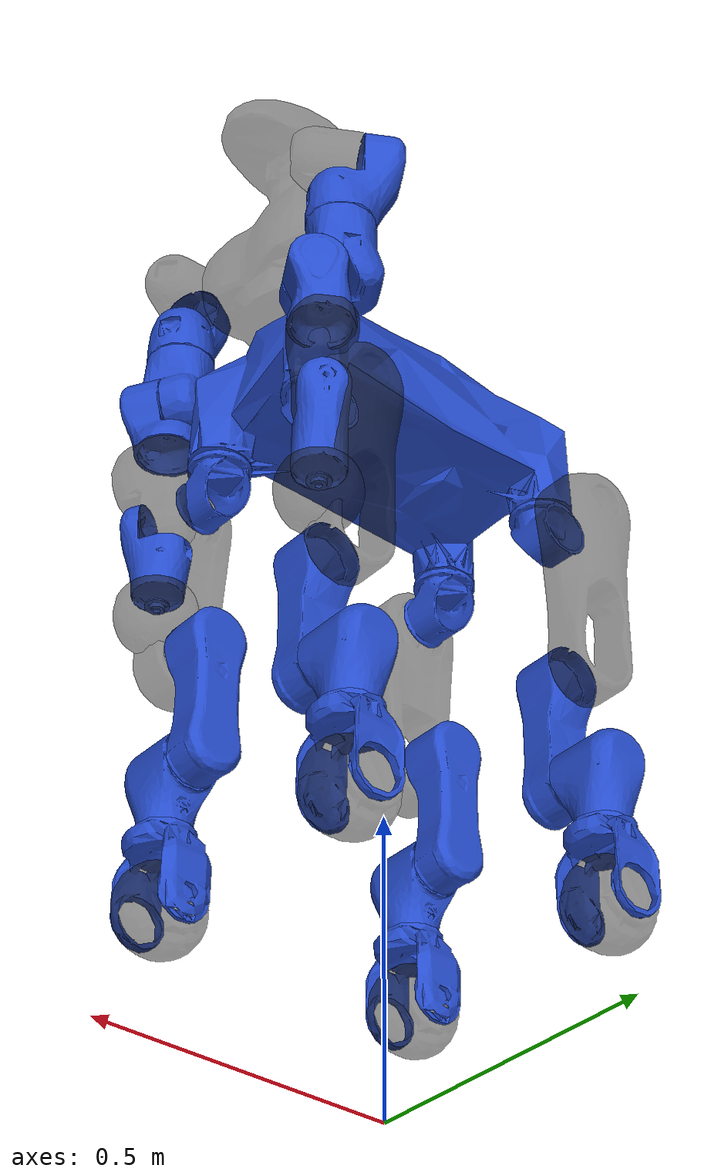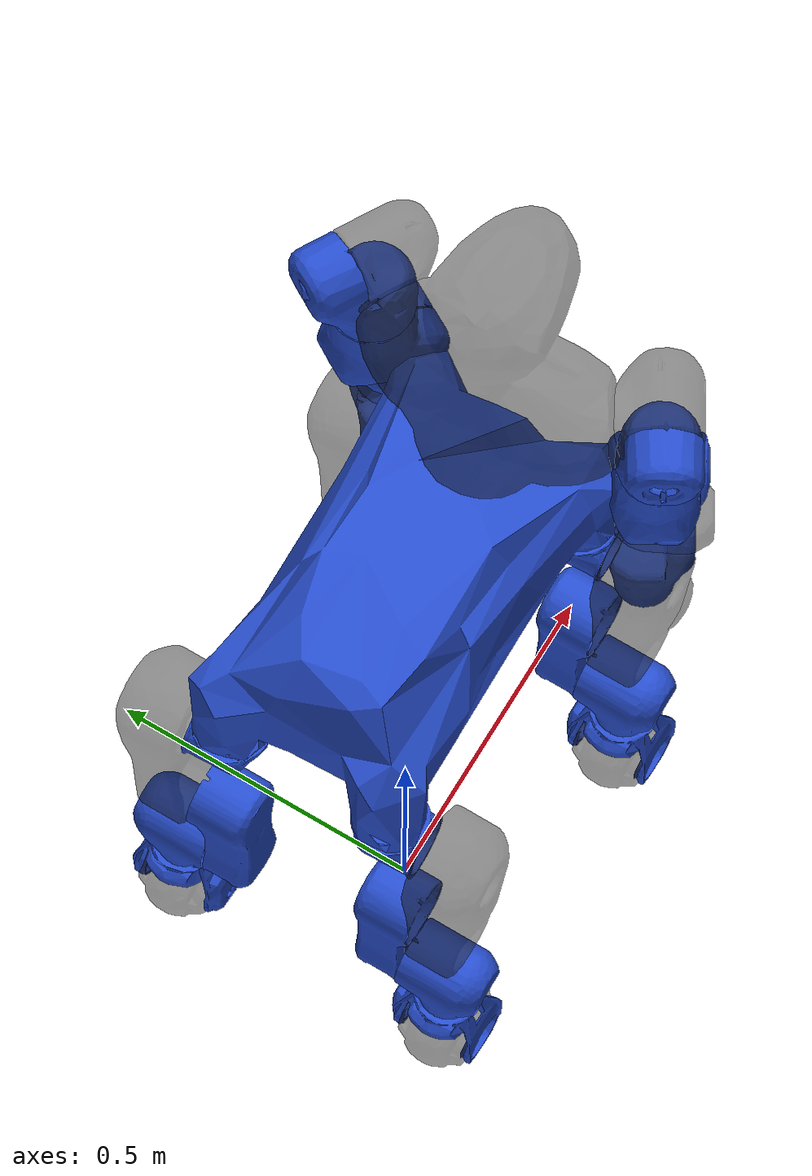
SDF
<sdf version='1.6'>
  <model name='centauro'>
    <link name='pelvis'>
      <pose frame=''>0 0 0 0 -0 0</pose>
      <inertial>
        <pose frame=''>0.001389 -0.001599 0.063101 0 -0 0</pose>
        <mass>16.0976</mass>
        <inertia>
          <ixx>0.239126</ixx>
          <ixy>-0.00505413</ixy>
          <ixz>-0.0197461</ixz>
          <iyy>0.714301</iyy>
          <iyz>0.00021312</iyz>
          <izz>0.818704</izz>
        </inertia>
      </inertial>
      <collision name='pelvis_collision'>
        <pose frame=''>0 0 0 0 -0 0</pose>
        <geometry>
          <mesh>
            <scale>0.001 0.001 0.001</scale>
            <uri>model://centauro_urdf/meshes/simple/pelvis.stl</uri>
          </mesh>
        </geometry>
        <surface>
          <contact>
            <ode/>
          </contact>
          <friction>
            <ode/>
          </friction>
        </surface>
      </collision>
      <visual name='pelvis_visual'>
        <pose frame=''>0 0 0 0 -0 0</pose>
        <geometry>
          <mesh>
            <scale>0.001 0.001 0.001</scale>
            <uri>model://centauro_urdf/meshes/pelvis.stl</uri>
          </mesh>
        </geometry>
        <material>
          <script>
            <name>Gazebo/LightBlueLaser</name>
            <uri>file://media/materials/scripts/gazebo.material</uri>
          </script>
        </material>
      </visual>
      <velocity_decay/>
      <gravity>1</gravity>
      <velocity_decay/>
      <sensor name='imu_link' type='imu'>
        <always_on>1</always_on>
        <update_rate>500</update_rate>
        <visualize>1</visualize>
        <topic>__default_topic__</topic>
        <imu>
          <angular_velocity/>
          <linear_acceleration/>
        </imu>
        <pose frame=''>0.248316 0 0.015 0 -0 0</pose>
      </sensor>
    </link>
    <link name='hip1_1'>
      <pose frame=''>0.25 0.125 -0.0566 -3.14159 -0 0.461416</pose>
      <inertial>
        <pose frame=''>0.010214 -0.018348 0.038091 0 -0 0</pose>
        <mass>1.91944</mass>
        <inertia>
          <ixx>0.00474396</ixx>
          <ixy>0.000574705</ixy>
          <ixz>-0.000378414</ixz>
          <iyy>0.00405519</iyy>
          <iyz>0.000740751</iyz>
          <izz>0.00341462</izz>
        </inertia>
      </inertial>
      <collision name='hip1_1_collision'>
        <pose frame=''>0 0 0 0 -0 -2.21876</pose>
        <geometry>
          <mesh>
            <scale>0.001 0.001 0.001</scale>
            <uri>model://centauro_urdf/meshes/simple/hip-yaw.stl</uri>
          </mesh>
        </geometry>
        <surface>
          <contact>
            <ode/>
          </contact>
          <friction>
            <ode/>
          </friction>
        </surface>
      </collision>
      <visual name='hip1_1_visual'>
        <pose frame=''>0 0 0 0 -0 -2.21876</pose>
        <geometry>
          <mesh>
            <scale>0.001 0.001 0.001</scale>
            <uri>model://centauro_urdf/meshes/hip-yaw.stl</uri>
          </mesh>
        </geometry>
        <material>
          <script>
            <name>Gazebo/LightBlueLaser</name>
            <uri>file://media/materials/scripts/gazebo.material</uri>
          </script>
        </material>
      </visual>
      <gravity>1</gravity>
      <velocity_decay/>
    </link>
    <joint name='hip_yaw_1' type='revolute'>
      <child>hip1_1</child>
      <parent>pelvis</parent>
      <axis>
        <xyz>-0 0 -1</xyz>
        <limit>
          <lower>-2.03</lower>
          <upper>2.51</upper>
          <effort>304</effort>
          <velocity>8.8</velocity>
        </limit>
        <dynamics>
          <spring_reference>0</spring_reference>
          <spring_stiffness>0</spring_stiffness>
        </dynamics>
        <use_parent_model_frame>1</use_parent_model_frame>
      </axis>
      <physics>
        <provide_feedback>1</provide_feedback>
        <ode>
          <provide_feedback>1</provide_feedback>
          <implicit_spring_damper>1</implicit_spring_damper>
          <cfm_damping>1</cfm_damping>
          <limit>
            <cfm>0</cfm>
            <erp>0.2</erp>
          </limit>
        </ode>
      </physics>
    </joint>
    <link name='hip2_1'>
      <pose frame=''>0.25 0.125 -0.1191 -1.5708 0 -0</pose>
      <inertial>
        <pose frame=''>2.6e-05 0.181027 0.08567 0 -0 0</pose>
        <mass>2.72645</mass>
        <inertia>
          <ixx>0.0485187</ixx>
          <ixy>-4.11894e-05</ixy>
          <ixz>-1.68778e-05</ixz>
          <iyy>0.00424205</iyy>
          <iyz>0.00322432</iyz>
          <izz>0.0482558</izz>
        </inertia>
      </inertial>
      <collision name='hip2_1_collision'>
        <pose frame=''>0 0 0 0 -0 0</pose>
        <geometry>
          <mesh>
            <scale>0.001 0.001 0.001</scale>
            <uri>model://centauro_urdf/meshes/simple/hip-pitch.stl</uri>
          </mesh>
        </geometry>
        <surface>
          <contact>
            <ode/>
          </contact>
          <friction>
            <ode/>
          </friction>
        </surface>
      </collision>
      <visual name='hip2_1_visual'>
        <pose frame=''>0 0 0 0 -0 0</pose>
        <geometry>
          <mesh>
            <scale>0.001 0.001 0.001</scale>
            <uri>model://centauro_urdf/meshes/hip-pitch.stl</uri>
          </mesh>
        </geometry>
        <material>
          <script>
            <name>Gazebo/BlackTransparent</name>
            <uri>file://media/materials/scripts/gazebo.material</uri>
          </script>
        </material>
      </visual>
      <gravity>1</gravity>
      <velocity_decay/>
    </link>
    <joint name='hip_pitch_1' type='revolute'>
      <child>hip2_1</child>
      <parent>hip1_1</parent>
      <axis>
        <xyz>0 1 -0</xyz>
        <limit>
          <lower>-2.0226</lower>
          <upper>2.02748</upper>
          <effort>304</effort>
          <velocity>8.8</velocity>
        </limit>
        <dynamics>
          <spring_reference>0</spring_reference>
          <spring_stiffness>0</spring_stiffness>
        </dynamics>
        <use_parent_model_frame>1</use_parent_model_frame>
      </axis>
      <physics>
        <provide_feedback>1</provide_feedback>
        <ode>
          <provide_feedback>1</provide_feedback>
          <implicit_spring_damper>1</implicit_spring_damper>
          <cfm_damping>1</cfm_damping>
          <limit>
            <cfm>0</cfm>
            <erp>0.2</erp>
          </limit>
        </ode>
      </physics>
    </joint>
    <link name='knee_1'>
      <pose frame=''>0.25 0.1214 -0.4191 -1.57079 1.57079 3.14159</pose>
      <inertial>
        <pose frame=''>0.108817 0.000109 -0.022639 0 -0 0</pose>
        <mass>1.93568</mass>
        <inertia>
          <ixx>0.00305342</ixx>
          <ixy>-4.22079e-05</ixy>
          <ixz>0.00136793</ixz>
          <iyy>0.0196033</iyy>
          <iyz>6.9941e-06</iyz>
          <izz>0.0198498</izz>
        </inertia>
      </inertial>
      <collision name='knee_1_collision'>
        <pose frame=''>0 0 0 0 -0 0</pose>
        <geometry>
          <mesh>
            <scale>0.001 0.001 0.001</scale>
            <uri>model://centauro_urdf/meshes/simple/knee.stl</uri>
          </mesh>
        </geometry>
        <surface>
          <contact>
            <ode/>
          </contact>
          <friction>
            <ode/>
          </friction>
        </surface>
      </collision>
      <visual name='knee_1_visual'>
        <pose frame=''>0 0 0 0 -0 0</pose>
        <geometry>
          <mesh>
            <scale>0.001 0.001 0.001</scale>
            <uri>model://centauro_urdf/meshes/knee.stl</uri>
          </mesh>
        </geometry>
        <material>
          <script>
            <name>Gazebo/LightBlueLaser</name>
            <uri>file://media/materials/scripts/gazebo.material</uri>
          </script>
        </material>
      </visual>
      <gravity>1</gravity>
      <velocity_decay/>
    </link>
    <joint name='knee_pitch_1' type='revolute'>
      <child>knee_1</child>
      <parent>hip2_1</parent>
      <axis>
        <xyz>-0 -1 0</xyz>
        <limit>
          <lower>-2.4056</lower>
          <upper>2.3994</upper>
          <effort>304</effort>
          <velocity>8.8</velocity>
        </limit>
        <dynamics>
          <spring_reference>0</spring_reference>
          <spring_stiffness>0</spring_stiffness>
        </dynamics>
        <use_parent_model_frame>1</use_parent_model_frame>
      </axis>
      <physics>
        <provide_feedback>1</provide_feedback>
        <ode>
          <provide_feedback>1</provide_feedback>
          <implicit_spring_damper>1</implicit_spring_damper>
          <cfm_damping>1</cfm_damping>
          <limit>
            <cfm>0</cfm>
            <erp>0.2</erp>
          </limit>
        </ode>
      </physics>
    </joint>
    <link name='ankle1_1'>
      <pose frame=''>0.25 0.22155 -0.6191 1.57079 1.57079 3.14159</pose>
      <inertial>
        <pose frame=''>0.032137 9.7e-05 -0.004422 0 -0 0</pose>
        <mass>1.23807</mass>
        <inertia>
          <ixx>0.00156105</ixx>
          <ixy>3.30597e-05</ixy>
          <ixz>-0.000131417</ixz>
          <iyy>0.00374232</iyy>
          <iyz>-2.12589e-05</iyz>
          <izz>0.00383124</izz>
        </inertia>
      </inertial>
      <collision name='ankle1_1_collision'>
        <pose frame=''>0 0 0 0 -0 0</pose>
        <geometry>
          <mesh>
            <scale>0.001 0.001 0.001</scale>
            <uri>model://centauro_urdf/meshes/simple/ankle-pitch.stl</uri>
          </mesh>
        </geometry>
        <surface>
          <contact>
            <ode/>
          </contact>
          <friction>
            <ode/>
          </friction>
        </surface>
      </collision>
      <visual name='ankle1_1_visual'>
        <pose frame=''>0 0 0 0 -0 0</pose>
        <geometry>
          <mesh>
            <scale>0.001 0.001 0.001</scale>
            <uri>model://centauro_urdf/meshes/ankle-pitch.stl</uri>
          </mesh>
        </geometry>
        <material>
          <script>
            <name>Gazebo/LightBlueLaser</name>
            <uri>file://media/materials/scripts/gazebo.material</uri>
          </script>
        </material>
      </visual>
      <gravity>1</gravity>
      <velocity_decay/>
    </link>
    <joint name='ankle_pitch_1' type='revolute'>
      <child>ankle1_1</child>
      <parent>knee_1</parent>
      <axis>
        <xyz>0 1 -0</xyz>
        <limit>
          <lower>-2.4056</lower>
          <upper>2.3184</upper>
          <effort>147</effort>
          <velocity>8.1</velocity>
        </limit>
        <dynamics>
          <spring_reference>0</spring_reference>
          <spring_stiffness>0</spring_stiffness>
        </dynamics>
        <use_parent_model_frame>1</use_parent_model_frame>
      </axis>
      <physics>
        <provide_feedback>1</provide_feedback>
        <ode>
          <provide_feedback>1</provide_feedback>
          <implicit_spring_damper>1</implicit_spring_damper>
          <cfm_damping>1</cfm_damping>
          <limit>
            <cfm>0</cfm>
            <erp>0.2</erp>
          </limit>
        </ode>
      </physics>
    </joint>
    <link name='ankle2_1'>
      <pose frame=''>0.25 0.22155 -0.6191 3.14159 0 3.14159</pose>
      <inertial>
        <pose frame=''>0.000444 0.000439 0.193921 0 -0 0</pose>
        <mass>1.15659</mass>
        <inertia>
          <ixx>0.00490195</ixx>
          <ixy>4.3032e-06</ixy>
          <ixz>3.46491e-05</ixz>
          <iyy>0.00387242</iyy>
          <iyz>1.7099e-05</iyz>
          <izz>0.00217832</izz>
        </inertia>
      </inertial>
      <collision name='ankle2_1_collision'>
        <pose frame=''>0 0 0 0 -0 0</pose>
        <geometry>
          <mesh>
            <scale>0.001 0.001 0.001</scale>
            <uri>model://centauro_urdf/meshes/simple/ankle-yaw.stl</uri>
          </mesh>
        </geometry>
        <surface>
          <contact>
            <ode/>
          </contact>
          <friction>
            <ode/>
          </friction>
        </surface>
      </collision>
      <visual name='ankle2_1_visual'>
        <pose frame=''>0 0 0 0 -0 0</pose>
        <geometry>
          <mesh>
            <scale>0.001 0.001 0.001</scale>
            <uri>model://centauro_urdf/meshes/ankle-yaw.stl</uri>
          </mesh>
        </geometry>
        <material>
          <script>
            <name>Gazebo/LightBlueLaser</name>
            <uri>file://media/materials/scripts/gazebo.material</uri>
          </script>
        </material>
      </visual>
      <gravity>1</gravity>
      <velocity_decay/>
    </link>
    <joint name='ankle_yaw_1' type='revolute'>
      <child>ankle2_1</child>
      <parent>ankle1_1</parent>
      <axis>
        <xyz>0 0 -1</xyz>
        <limit>
          <lower>-2.5626</lower>
          <upper>2.5384</upper>
          <effort>35</effort>
          <velocity>20</velocity>
        </limit>
        <dynamics>
          <spring_reference>0</spring_reference>
          <spring_stiffness>0</spring_stiffness>
        </dynamics>
        <use_parent_model_frame>1</use_parent_model_frame>
      </axis>
      <physics>
        <provide_feedback>1</provide_feedback>
        <ode>
          <provide_feedback>1</provide_feedback>
          <implicit_spring_damper>1</implicit_spring_damper>
          <cfm_damping>1</cfm_damping>
          <limit>
            <cfm>0</cfm>
            <erp>0.2</erp>
          </limit>
        </ode>
      </physics>
    </joint>
    <link name='wheel_1'>
      <pose frame=''>0.25 0.2224 -0.85645 -1.5708 -0 -0</pose>
      <inertial>
        <pose frame=''>0 0 0.002427 0 -0 0</pose>
        <mass>1.7289</mass>
        <inertia>
          <ixx>0.00468643</ixx>
          <ixy>0</ixy>
          <ixz>0</ixz>
          <iyy>0.00467135</iyy>
          <iyz>0</iyz>
          <izz>0.0053126</izz>
        </inertia>
      </inertial>
      <collision name='wheel_1_collision'>
        <pose frame=''>0 0 0 0 -0 0</pose>
        <geometry>
          <cylinder>
            <length>0.06</length>
            <radius>0.085</radius>
          </cylinder>
        </geometry>
        <surface>
          <contact>
            <ode>
              <kp>1e+06</kp>
              <kd>100</kd>
              <max_vel>1</max_vel>
              <min_depth>0</min_depth>
            </ode>
          </contact>
          <friction>
            <ode>
              <mu>1</mu>
              <mu2>1</mu2>
              <fdir1>1 0 0</fdir1>
            </ode>
          </friction>
        </surface>
      </collision>
      <visual name='wheel_1_visual'>
        <pose frame=''>0 0 0 0 -0 0</pose>
        <geometry>
          <mesh>
            <scale>0.001 0.001 0.001</scale>
            <uri>model://centauro_urdf/meshes/wheel.stl</uri>
          </mesh>
        </geometry>
        <material>
          <script>
            <name>Gazebo/BlackTransparent</name>
            <uri>file://media/materials/scripts/gazebo.material</uri>
          </script>
        </material>
      </visual>
      <velocity_decay/>
      <gravity>1</gravity>
      <velocity_decay/>
    </link>
    <joint name='j_wheel_1' type='revolute'>
      <child>wheel_1</child>
      <parent>ankle2_1</parent>
      <axis>
        <xyz>0 1 -0</xyz>
        <limit>
          <lower>-1e+16</lower>
          <upper>1e+16</upper>
        </limit>
        <dynamics>
          <spring_reference>0</spring_reference>
          <spring_stiffness>0</spring_stiffness>
        </dynamics>
        <use_parent_model_frame>1</use_parent_model_frame>
      </axis>
      <physics>
        <provide_feedback>1</provide_feedback>
        <ode>
          <provide_feedback>1</provide_feedback>
          <implicit_spring_damper>1</implicit_spring_damper>
          <cfm_damping>1</cfm_damping>
          <limit>
            <cfm>0</cfm>
            <erp>0.2</erp>
          </limit>
        </ode>
      </physics>
    </joint>
    <link name='hip1_2'>
      <pose frame=''>0.25 -0.125 -0.0566 -3.14159 -0 -0.461416</pose>
      <inertial>
        <pose frame=''>0.010214 0.018348 0.038091 0 -0 0</pose>
        <mass>1.91944</mass>
        <inertia>
          <ixx>0.00474396</ixx>
          <ixy>-0.000574705</ixy>
          <ixz>-0.000378414</ixz>
          <iyy>0.00405519</iyy>
          <iyz>-0.000740751</iyz>
          <izz>0.00341462</izz>
        </inertia>
      </inertial>
      <collision name='hip1_2_collision'>
        <pose frame=''>0 0 0 0 -0 0</pose>
        <geometry>
          <mesh>
            <scale>0.001 0.001 0.001</scale>
            <uri>model://centauro_urdf/meshes/simple/hip-yaw.stl</uri>
          </mesh>
        </geometry>
        <surface>
          <contact>
            <ode/>
          </contact>
          <friction>
            <ode/>
          </friction>
        </surface>
      </collision>
      <visual name='hip1_2_visual'>
        <pose frame=''>0 0 0 0 -0 0</pose>
        <geometry>
          <mesh>
            <scale>0.001 0.001 0.001</scale>
            <uri>model://centauro_urdf/meshes/hip-yaw.stl</uri>
          </mesh>
        </geometry>
        <material>
          <script>
            <name>Gazebo/LightBlueLaser</name>
            <uri>file://media/materials/scripts/gazebo.material</uri>
          </script>
        </material>
      </visual>
      <gravity>1</gravity>
      <velocity_decay/>
    </link>
    <joint name='hip_yaw_2' type='revolute'>
      <child>hip1_2</child>
      <parent>pelvis</parent>
      <axis>
        <xyz>0 0 -1</xyz>
        <limit>
          <lower>-2.51</lower>
          <upper>2.03</upper>
          <effort>304</effort>
          <velocity>8.8</velocity>
        </limit>
        <dynamics>
          <spring_reference>0</spring_reference>
          <spring_stiffness>0</spring_stiffness>
        </dynamics>
        <use_parent_model_frame>1</use_parent_model_frame>
      </axis>
      <physics>
        <provide_feedback>1</provide_feedback>
        <ode>
          <provide_feedback>1</provide_feedback>
          <implicit_spring_damper>1</implicit_spring_damper>
          <cfm_damping>1</cfm_damping>
          <limit>
            <cfm>0</cfm>
            <erp>0.2</erp>
          </limit>
        </ode>
      </physics>
    </joint>
    <link name='hip2_2'>
      <pose frame=''>0.25 -0.125 -0.1191 -1.5708 0 -3.14159</pose>
      <inertial>
        <pose frame=''>2.6e-05 0.181027 0.08567 0 -0 0</pose>
        <mass>2.72645</mass>
        <inertia>
          <ixx>0.0485187</ixx>
          <ixy>-4.11894e-05</ixy>
          <ixz>-1.68778e-05</ixz>
          <iyy>0.00424205</iyy>
          <iyz>0.00322432</iyz>
          <izz>0.0482558</izz>
        </inertia>
      </inertial>
      <collision name='hip2_2_collision'>
        <pose frame=''>0 0 0 0 -0 0</pose>
        <geometry>
          <mesh>
            <scale>0.001 0.001 0.001</scale>
            <uri>model://centauro_urdf/meshes/simple/hip-pitch.stl</uri>
          </mesh>
        </geometry>
        <surface>
          <contact>
            <ode/>
          </contact>
          <friction>
            <ode/>
          </friction>
        </surface>
      </collision>
      <visual name='hip2_2_visual'>
        <pose frame=''>0 0 0 0 -0 0</pose>
        <geometry>
          <mesh>
            <scale>0.001 0.001 0.001</scale>
            <uri>model://centauro_urdf/meshes/hip-pitch.stl</uri>
          </mesh>
        </geometry>
        <material>
          <script>
            <name>Gazebo/BlackTransparent</name>
            <uri>file://media/materials/scripts/gazebo.material</uri>
          </script>
        </material>
      </visual>
      <gravity>1</gravity>
      <velocity_decay/>
    </link>
    <joint name='hip_pitch_2' type='revolute'>
      <child>hip2_2</child>
      <parent>hip1_2</parent>
      <axis>
        <xyz>0 -1 -0</xyz>
        <limit>
          <lower>-2.0156</lower>
          <upper>2.0354</upper>
          <effort>304</effort>
          <velocity>8.8</velocity>
        </limit>
        <dynamics>
          <spring_reference>0</spring_reference>
          <spring_stiffness>0</spring_stiffness>
        </dynamics>
        <use_parent_model_frame>1</use_parent_model_frame>
      </axis>
      <physics>
        <provide_feedback>1</provide_feedback>
        <ode>
          <provide_feedback>1</provide_feedback>
          <implicit_spring_damper>1</implicit_spring_damper>
          <cfm_damping>1</cfm_damping>
          <limit>
            <cfm>0</cfm>
            <erp>0.2</erp>
          </limit>
        </ode>
      </physics>
    </joint>
    <link name='knee_2'>
      <pose frame=''>0.25 -0.1214 -0.4191 1.57079 1.57079 3.14159</pose>
      <inertial>
        <pose frame=''>0.108817 0.000109 -0.022639 0 -0 0</pose>
        <mass>1.93568</mass>
        <inertia>
          <ixx>0.00305342</ixx>
          <ixy>-4.22079e-05</ixy>
          <ixz>0.00136793</ixz>
          <iyy>0.0196033</iyy>
          <iyz>6.9941e-06</iyz>
          <izz>0.0198498</izz>
        </inertia>
      </inertial>
      <collision name='knee_2_collision'>
        <pose frame=''>0 0 0 0 -0 0</pose>
        <geometry>
          <mesh>
            <scale>0.001 0.001 0.001</scale>
            <uri>model://centauro_urdf/meshes/simple/knee.stl</uri>
          </mesh>
        </geometry>
        <surface>
          <contact>
            <ode/>
          </contact>
          <friction>
            <ode/>
          </friction>
        </surface>
      </collision>
      <visual name='knee_2_visual'>
        <pose frame=''>0 0 0 0 -0 0</pose>
        <geometry>
          <mesh>
            <scale>0.001 0.001 0.001</scale>
            <uri>model://centauro_urdf/meshes/knee.stl</uri>
          </mesh>
        </geometry>
        <material>
          <script>
            <name>Gazebo/LightBlueLaser</name>
            <uri>file://media/materials/scripts/gazebo.material</uri>
          </script>
        </material>
      </visual>
      <gravity>1</gravity>
      <velocity_decay/>
    </link>
    <joint name='knee_pitch_2' type='revolute'>
      <child>knee_2</child>
      <parent>hip2_2</parent>
      <axis>
        <xyz>-0 1 0</xyz>
        <limit>
          <lower>-2.4006</lower>
          <upper>2.4034</upper>
          <effort>304</effort>
          <velocity>8.8</velocity>
        </limit>
        <dynamics>
          <spring_reference>0</spring_reference>
          <spring_stiffness>0</spring_stiffness>
        </dynamics>
        <use_parent_model_frame>1</use_parent_model_frame>
      </axis>
      <physics>
        <provide_feedback>1</provide_feedback>
        <ode>
          <provide_feedback>1</provide_feedback>
          <implicit_spring_damper>1</implicit_spring_damper>
          <cfm_damping>1</cfm_damping>
          <limit>
            <cfm>0</cfm>
            <erp>0.2</erp>
          </limit>
        </ode>
      </physics>
    </joint>
    <link name='ankle1_2'>
      <pose frame=''>0.25 -0.22155 -0.6191 -1.57079 1.57079 3.14159</pose>
      <inertial>
        <pose frame=''>0.032137 9.7e-05 -0.004422 0 -0 0</pose>
        <mass>1.23807</mass>
        <inertia>
          <ixx>0.00156105</ixx>
          <ixy>3.30597e-05</ixy>
          <ixz>-0.000131417</ixz>
          <iyy>0.00374232</iyy>
          <iyz>-2.12589e-05</iyz>
          <izz>0.00383124</izz>
        </inertia>
      </inertial>
      <collision name='ankle1_2_collision'>
        <pose frame=''>0 0 0 0 -0 0</pose>
        <geometry>
          <mesh>
            <scale>0.001 0.001 0.001</scale>
            <uri>model://centauro_urdf/meshes/simple/ankle-pitch.stl</uri>
          </mesh>
        </geometry>
        <surface>
          <contact>
            <ode/>
          </contact>
          <friction>
            <ode/>
          </friction>
        </surface>
      </collision>
      <visual name='ankle1_2_visual'>
        <pose frame=''>0 0 0 0 -0 0</pose>
        <geometry>
          <mesh>
            <scale>0.001 0.001 0.001</scale>
            <uri>model://centauro_urdf/meshes/ankle-pitch.stl</uri>
          </mesh>
        </geometry>
        <material>
          <script>
            <name>Gazebo/LightBlueLaser</name>
            <uri>file://media/materials/scripts/gazebo.material</uri>
          </script>
        </material>
      </visual>
      <gravity>1</gravity>
      <velocity_decay/>
    </link>
    <joint name='ankle_pitch_2' type='revolute'>
      <child>ankle1_2</child>
      <parent>knee_2</parent>
      <axis>
        <xyz>0 -1 -0</xyz>
        <limit>
          <lower>-2.3266</lower>
          <upper>2.3914</upper>
          <effort>147</effort>
          <velocity>8.1</velocity>
        </limit>
        <dynamics>
          <spring_reference>0</spring_reference>
          <spring_stiffness>0</spring_stiffness>
        </dynamics>
        <use_parent_model_frame>1</use_parent_model_frame>
      </axis>
      <physics>
        <provide_feedback>1</provide_feedback>
        <ode>
          <provide_feedback>1</provide_feedback>
          <implicit_spring_damper>1</implicit_spring_damper>
          <cfm_damping>1</cfm_damping>
          <limit>
            <cfm>0</cfm>
            <erp>0.2</erp>
          </limit>
        </ode>
      </physics>
    </joint>
    <link name='ankle2_2'>
      <pose frame=''>0.25 -0.22155 -0.6191 -3.14159 0 0</pose>
      <inertial>
        <pose frame=''>0.000444 0.000439 0.193921 0 -0 0</pose>
        <mass>1.15659</mass>
        <inertia>
          <ixx>0.00490195</ixx>
          <ixy>4.3032e-06</ixy>
          <ixz>3.46491e-05</ixz>
          <iyy>0.00387242</iyy>
          <iyz>1.7099e-05</iyz>
          <izz>0.00217832</izz>
        </inertia>
      </inertial>
      <collision name='ankle2_2_collision'>
        <pose frame=''>0 0 0 0 -0 0</pose>
        <geometry>
          <mesh>
            <scale>0.001 0.001 0.001</scale>
            <uri>model://centauro_urdf/meshes/simple/ankle-yaw.stl</uri>
          </mesh>
        </geometry>
        <surface>
          <contact>
            <ode/>
          </contact>
          <friction>
            <ode/>
          </friction>
        </surface>
      </collision>
      <visual name='ankle2_2_visual'>
        <pose frame=''>0 0 0 0 -0 0</pose>
        <geometry>
          <mesh>
            <scale>0.001 0.001 0.001</scale>
            <uri>model://centauro_urdf/meshes/ankle-yaw.stl</uri>
          </mesh>
        </geometry>
        <material>
          <script>
            <name>Gazebo/LightBlueLaser</name>
            <uri>file://media/materials/scripts/gazebo.material</uri>
          </script>
        </material>
      </visual>
      <gravity>1</gravity>
      <velocity_decay/>
    </link>
    <joint name='ankle_yaw_2' type='revolute'>
      <child>ankle2_2</child>
      <parent>ankle1_2</parent>
      <axis>
        <xyz>-0 0 -1</xyz>
        <limit>
          <lower>-2.5546</lower>
          <upper>2.5484</upper>
          <effort>35</effort>
          <velocity>20</velocity>
        </limit>
        <dynamics>
          <spring_reference>0</spring_reference>
          <spring_stiffness>0</spring_stiffness>
        </dynamics>
        <use_parent_model_frame>1</use_parent_model_frame>
      </axis>
      <physics>
        <provide_feedback>1</provide_feedback>
        <ode>
          <provide_feedback>1</provide_feedback>
          <implicit_spring_damper>1</implicit_spring_damper>
          <cfm_damping>1</cfm_damping>
          <limit>
            <cfm>0</cfm>
            <erp>0.2</erp>
          </limit>
        </ode>
      </physics>
    </joint>
    <link name='wheel_2'>
      <pose frame=''>0.25 -0.2224 -0.85645 -1.5708 -0 -3.14159</pose>
      <inertial>
        <pose frame=''>0 0 0.002427 0 -0 0</pose>
        <mass>1.7289</mass>
        <inertia>
          <ixx>0.00468643</ixx>
          <ixy>0</ixy>
          <ixz>0</ixz>
          <iyy>0.00467135</iyy>
          <iyz>0</iyz>
          <izz>0.0053126</izz>
        </inertia>
      </inertial>
      <collision name='wheel_2_collision'>
        <pose frame=''>0 0 0 0 -0 0</pose>
        <geometry>
          <cylinder>
            <length>0.06</length>
            <radius>0.085</radius>
          </cylinder>
        </geometry>
        <surface>
          <contact>
            <ode>
              <kp>1e+06</kp>
              <kd>100</kd>
              <max_vel>1</max_vel>
              <min_depth>0</min_depth>
            </ode>
          </contact>
          <friction>
            <ode>
              <mu>1</mu>
              <mu2>1</mu2>
              <fdir1>1 0 0</fdir1>
            </ode>
          </friction>
        </surface>
      </collision>
      <visual name='wheel_2_visual'>
        <pose frame=''>0 0 0 0 -0 0</pose>
        <geometry>
          <mesh>
            <scale>0.001 0.001 0.001</scale>
            <uri>model://centauro_urdf/meshes/wheel.stl</uri>
          </mesh>
        </geometry>
        <material>
          <script>
            <name>Gazebo/BlackTransparent</name>
            <uri>file://media/materials/scripts/gazebo.material</uri>
          </script>
        </material>
      </visual>
      <velocity_decay/>
      <gravity>1</gravity>
      <velocity_decay/>
    </link>
    <joint name='j_wheel_2' type='revolute'>
      <child>wheel_2</child>
      <parent>ankle2_2</parent>
      <axis>
        <xyz>0 -1 -0</xyz>
        <limit>
          <lower>-1e+16</lower>
          <upper>1e+16</upper>
        </limit>
        <dynamics>
          <spring_reference>0</spring_reference>
          <spring_stiffness>0</spring_stiffness>
        </dynamics>
        <use_parent_model_frame>1</use_parent_model_frame>
      </axis>
      <physics>
        <provide_feedback>1</provide_feedback>
        <ode>
          <provide_feedback>1</provide_feedback>
          <implicit_spring_damper>1</implicit_spring_damper>
          <cfm_damping>1</cfm_damping>
          <limit>
            <cfm>0</cfm>
            <erp>0.2</erp>
          </limit>
        </ode>
      </physics>
    </joint>
    <link name='hip1_3'>
      <pose frame=''>-0.25 0.125 -0.0566 -3.14159 -0 2.68018</pose>
      <inertial>
        <pose frame=''>0.010214 0.018348 0.038091 0 -0 0</pose>
        <mass>1.91944</mass>
        <inertia>
          <ixx>0.00474396</ixx>
          <ixy>-0.000574705</ixy>
          <ixz>-0.000378414</ixz>
          <iyy>0.00405519</iyy>
          <iyz>-0.000740751</iyz>
          <izz>0.00341462</izz>
        </inertia>
      </inertial>
      <collision name='hip1_3_collision'>
        <pose frame=''>0 0 0 0 -0 0</pose>
        <geometry>
          <mesh>
            <scale>0.001 0.001 0.001</scale>
            <uri>model://centauro_urdf/meshes/simple/hip-yaw.stl</uri>
          </mesh>
        </geometry>
        <surface>
          <contact>
            <ode/>
          </contact>
          <friction>
            <ode/>
          </friction>
        </surface>
      </collision>
      <visual name='hip1_3_visual'>
        <pose frame=''>0 0 0 0 -0 0</pose>
        <geometry>
          <mesh>
            <scale>0.001 0.001 0.001</scale>
            <uri>model://centauro_urdf/meshes/hip-yaw.stl</uri>
          </mesh>
        </geometry>
        <material>
          <script>
            <name>Gazebo/LightBlueLaser</name>
            <uri>file://media/materials/scripts/gazebo.material</uri>
          </script>
        </material>
      </visual>
      <gravity>1</gravity>
      <velocity_decay/>
    </link>
    <joint name='hip_yaw_3' type='revolute'>
      <child>hip1_3</child>
      <parent>pelvis</parent>
      <axis>
        <xyz>-0 -0 -1</xyz>
        <limit>
          <lower>-2.51</lower>
          <upper>2.03</upper>
          <effort>304</effort>
          <velocity>8.8</velocity>
        </limit>
        <dynamics>
          <spring_reference>0</spring_reference>
          <spring_stiffness>0</spring_stiffness>
        </dynamics>
        <use_parent_model_frame>1</use_parent_model_frame>
      </axis>
      <physics>
        <provide_feedback>1</provide_feedback>
        <ode>
          <provide_feedback>1</provide_feedback>
          <implicit_spring_damper>1</implicit_spring_damper>
          <cfm_damping>1</cfm_damping>
          <limit>
            <cfm>0</cfm>
            <erp>0.2</erp>
          </limit>
        </ode>
      </physics>
    </joint>
    <link name='hip2_3'>
      <pose frame=''>-0.25 0.125 -0.1191 -1.5708 0 0</pose>
      <inertial>
        <pose frame=''>2.6e-05 0.181027 0.08567 0 -0 0</pose>
        <mass>2.72645</mass>
        <inertia>
          <ixx>0.0485187</ixx>
          <ixy>-4.11894e-05</ixy>
          <ixz>-1.68778e-05</ixz>
          <iyy>0.00424205</iyy>
          <iyz>0.00322432</iyz>
          <izz>0.0482558</izz>
        </inertia>
      </inertial>
      <collision name='hip2_3_collision'>
        <pose frame=''>0 0 0 0 -0 0</pose>
        <geometry>
          <mesh>
            <scale>0.001 0.001 0.001</scale>
            <uri>model://centauro_urdf/meshes/simple/hip-pitch.stl</uri>
          </mesh>
        </geometry>
        <surface>
          <contact>
            <ode/>
          </contact>
          <friction>
            <ode/>
          </friction>
        </surface>
      </collision>
      <visual name='hip2_3_visual'>
        <pose frame=''>0 0 0 0 -0 0</pose>
        <geometry>
          <mesh>
            <scale>0.001 0.001 0.001</scale>
            <uri>model://centauro_urdf/meshes/hip-pitch.stl</uri>
          </mesh>
        </geometry>
        <material>
          <script>
            <name>Gazebo/BlackTransparent</name>
            <uri>file://media/materials/scripts/gazebo.material</uri>
          </script>
        </material>
      </visual>
      <gravity>1</gravity>
      <velocity_decay/>
    </link>
    <joint name='hip_pitch_3' type='revolute'>
      <child>hip2_3</child>
      <parent>hip1_3</parent>
      <axis>
        <xyz>-0 1 -0</xyz>
        <limit>
          <lower>-2.0126</lower>
          <upper>2.0384</upper>
          <effort>304</effort>
          <velocity>8.8</velocity>
        </limit>
        <dynamics>
          <spring_reference>0</spring_reference>
          <spring_stiffness>0</spring_stiffness>
        </dynamics>
        <use_parent_model_frame>1</use_parent_model_frame>
      </axis>
      <physics>
        <provide_feedback>1</provide_feedback>
        <ode>
          <provide_feedback>1</provide_feedback>
          <implicit_spring_damper>1</implicit_spring_damper>
          <cfm_damping>1</cfm_damping>
          <limit>
            <cfm>0</cfm>
            <erp>0.2</erp>
          </limit>
        </ode>
      </physics>
    </joint>
    <link name='knee_3'>
      <pose frame=''>-0.25 0.1214 -0.4191 -1.57079 1.57079 3.14159</pose>
      <inertial>
        <pose frame=''>0.108817 0.000109 -0.022639 0 -0 0</pose>
        <mass>1.93568</mass>
        <inertia>
          <ixx>0.00305342</ixx>
          <ixy>-4.22079e-05</ixy>
          <ixz>0.00136793</ixz>
          <iyy>0.0196033</iyy>
          <iyz>6.9941e-06</iyz>
          <izz>0.0198498</izz>
        </inertia>
      </inertial>
      <collision name='knee_3_collision'>
        <pose frame=''>0 0 0 0 -0 0</pose>
        <geometry>
          <mesh>
            <scale>0.001 0.001 0.001</scale>
            <uri>model://centauro_urdf/meshes/simple/knee.stl</uri>
          </mesh>
        </geometry>
        <surface>
          <contact>
            <ode/>
          </contact>
          <friction>
            <ode/>
          </friction>
        </surface>
      </collision>
      <visual name='knee_3_visual'>
        <pose frame=''>0 0 0 0 -0 0</pose>
        <geometry>
          <mesh>
            <scale>0.001 0.001 0.001</scale>
            <uri>model://centauro_urdf/meshes/knee.stl</uri>
          </mesh>
        </geometry>
        <material>
          <script>
            <name>Gazebo/LightBlueLaser</name>
            <uri>file://media/materials/scripts/gazebo.material</uri>
          </script>
        </material>
      </visual>
      <gravity>1</gravity>
      <velocity_decay/>
    </link>
    <joint name='knee_pitch_3' type='revolute'>
      <child>knee_3</child>
      <parent>hip2_3</parent>
      <axis>
        <xyz>-0 -1 0</xyz>
        <limit>
          <lower>-2.4056</lower>
          <upper>2.4064</upper>
          <effort>304</effort>
          <velocity>8.8</velocity>
        </limit>
        <dynamics>
          <spring_reference>0</spring_reference>
          <spring_stiffness>0</spring_stiffness>
        </dynamics>
        <use_parent_model_frame>1</use_parent_model_frame>
      </axis>
      <physics>
        <provide_feedback>1</provide_feedback>
        <ode>
          <provide_feedback>1</provide_feedback>
          <implicit_spring_damper>1</implicit_spring_damper>
          <cfm_damping>1</cfm_damping>
          <limit>
            <cfm>0</cfm>
            <erp>0.2</erp>
          </limit>
        </ode>
      </physics>
    </joint>
    <link name='ankle1_3'>
      <pose frame=''>-0.25 0.22155 -0.6191 1.57079 1.57079 3.14159</pose>
      <inertial>
        <pose frame=''>0.032137 9.7e-05 -0.004422 0 -0 0</pose>
        <mass>1.23807</mass>
        <inertia>
          <ixx>0.00156105</ixx>
          <ixy>3.30597e-05</ixy>
          <ixz>-0.000131417</ixz>
          <iyy>0.00374232</iyy>
          <iyz>-2.12589e-05</iyz>
          <izz>0.00383124</izz>
        </inertia>
      </inertial>
      <collision name='ankle1_3_collision'>
        <pose frame=''>0 0 0 0 -0 0</pose>
        <geometry>
          <mesh>
            <scale>0.001 0.001 0.001</scale>
            <uri>model://centauro_urdf/meshes/simple/ankle-pitch.stl</uri>
          </mesh>
        </geometry>
        <surface>
          <contact>
            <ode/>
          </contact>
          <friction>
            <ode/>
          </friction>
        </surface>
      </collision>
      <visual name='ankle1_3_visual'>
        <pose frame=''>0 0 0 0 -0 0</pose>
        <geometry>
          <mesh>
            <scale>0.001 0.001 0.001</scale>
            <uri>model://centauro_urdf/meshes/ankle-pitch.stl</uri>
          </mesh>
        </geometry>
        <material>
          <script>
            <name>Gazebo/LightBlueLaser</name>
            <uri>file://media/materials/scripts/gazebo.material</uri>
          </script>
        </material>
      </visual>
      <gravity>1</gravity>
      <velocity_decay/>
    </link>
    <joint name='ankle_pitch_3' type='revolute'>
      <child>ankle1_3</child>
      <parent>knee_3</parent>
      <axis>
        <xyz>0 1 -0</xyz>
        <limit>
          <lower>-2.4696</lower>
          <upper>2.4464</upper>
          <effort>147</effort>
          <velocity>8.1</velocity>
        </limit>
        <dynamics>
          <spring_reference>0</spring_reference>
          <spring_stiffness>0</spring_stiffness>
        </dynamics>
        <use_parent_model_frame>1</use_parent_model_frame>
      </axis>
      <physics>
        <provide_feedback>1</provide_feedback>
        <ode>
          <provide_feedback>1</provide_feedback>
          <implicit_spring_damper>1</implicit_spring_damper>
          <cfm_damping>1</cfm_damping>
          <limit>
            <cfm>0</cfm>
            <erp>0.2</erp>
          </limit>
        </ode>
      </physics>
    </joint>
    <link name='ankle2_3'>
      <pose frame=''>-0.25 0.22155 -0.6191 -3.14159 0 3.14159</pose>
      <inertial>
        <pose frame=''>0.000444 0.000439 0.193921 0 -0 0</pose>
        <mass>1.15659</mass>
        <inertia>
          <ixx>0.00490195</ixx>
          <ixy>4.3032e-06</ixy>
          <ixz>3.46491e-05</ixz>
          <iyy>0.00387242</iyy>
          <iyz>1.7099e-05</iyz>
          <izz>0.00217832</izz>
        </inertia>
      </inertial>
      <collision name='ankle2_3_collision'>
        <pose frame=''>0 0 0 0 -0 0</pose>
        <geometry>
          <mesh>
            <scale>0.001 0.001 0.001</scale>
            <uri>model://centauro_urdf/meshes/simple/ankle-yaw.stl</uri>
          </mesh>
        </geometry>
        <surface>
          <contact>
            <ode/>
          </contact>
          <friction>
            <ode/>
          </friction>
        </surface>
      </collision>
      <visual name='ankle2_3_visual'>
        <pose frame=''>0 0 0 0 -0 0</pose>
        <geometry>
          <mesh>
            <scale>0.001 0.001 0.001</scale>
            <uri>model://centauro_urdf/meshes/ankle-yaw.stl</uri>
          </mesh>
        </geometry>
        <material>
          <script>
            <name>Gazebo/LightBlueLaser</name>
            <uri>file://media/materials/scripts/gazebo.material</uri>
          </script>
        </material>
      </visual>
      <gravity>1</gravity>
      <velocity_decay/>
    </link>
    <joint name='ankle_yaw_3' type='revolute'>
      <child>ankle2_3</child>
      <parent>ankle1_3</parent>
      <axis>
        <xyz>0 -0 -1</xyz>
        <limit>
          <lower>-2.5606</lower>
          <upper>2.5454</upper>
          <effort>35</effort>
          <velocity>20</velocity>
        </limit>
        <dynamics>
          <spring_reference>0</spring_reference>
          <spring_stiffness>0</spring_stiffness>
        </dynamics>
        <use_parent_model_frame>1</use_parent_model_frame>
      </axis>
      <physics>
        <provide_feedback>1</provide_feedback>
        <ode>
          <provide_feedback>1</provide_feedback>
          <implicit_spring_damper>1</implicit_spring_damper>
          <cfm_damping>1</cfm_damping>
          <limit>
            <cfm>0</cfm>
            <erp>0.2</erp>
          </limit>
        </ode>
      </physics>
    </joint>
    <link name='wheel_3'>
      <pose frame=''>-0.25 0.2224 -0.85645 -1.5708 -0 -0</pose>
      <inertial>
        <pose frame=''>0 0 0.002427 0 -0 0</pose>
        <mass>1.7289</mass>
        <inertia>
          <ixx>0.00468643</ixx>
          <ixy>0</ixy>
          <ixz>0</ixz>
          <iyy>0.00467135</iyy>
          <iyz>0</iyz>
          <izz>0.0053126</izz>
        </inertia>
      </inertial>
      <collision name='wheel_3_collision'>
        <pose frame=''>0 0 0 0 -0 0</pose>
        <geometry>
          <cylinder>
            <length>0.06</length>
            <radius>0.085</radius>
          </cylinder>
        </geometry>
        <surface>
          <contact>
            <ode>
              <kp>1e+06</kp>
              <kd>100</kd>
              <max_vel>1</max_vel>
              <min_depth>0</min_depth>
            </ode>
          </contact>
          <friction>
            <ode>
              <mu>1</mu>
              <mu2>1</mu2>
              <fdir1>1 0 0</fdir1>
            </ode>
          </friction>
        </surface>
      </collision>
      <visual name='wheel_3_visual'>
        <pose frame=''>0 0 0 0 -0 0</pose>
        <geometry>
          <mesh>
            <scale>0.001 0.001 0.001</scale>
            <uri>model://centauro_urdf/meshes/wheel.stl</uri>
          </mesh>
        </geometry>
        <material>
          <script>
            <name>Gazebo/BlackTransparent</name>
            <uri>file://media/materials/scripts/gazebo.material</uri>
          </script>
        </material>
      </visual>
      <velocity_decay/>
      <gravity>1</gravity>
      <velocity_decay/>
    </link>
    <joint name='j_wheel_3' type='revolute'>
      <child>wheel_3</child>
      <parent>ankle2_3</parent>
      <axis>
        <xyz>0 1 -0</xyz>
        <limit>
          <lower>-1e+16</lower>
          <upper>1e+16</upper>
        </limit>
        <dynamics>
          <spring_reference>0</spring_reference>
          <spring_stiffness>0</spring_stiffness>
        </dynamics>
        <use_parent_model_frame>1</use_parent_model_frame>
      </axis>
      <physics>
        <provide_feedback>1</provide_feedback>
        <ode>
          <provide_feedback>1</provide_feedback>
          <implicit_spring_damper>1</implicit_spring_damper>
          <cfm_damping>1</cfm_damping>
          <limit>
            <cfm>0</cfm>
            <erp>0.2</erp>
          </limit>
        </ode>
      </physics>
    </joint>
    <link name='hip1_4'>
      <pose frame=''>-0.25 -0.125 -0.0566 -3.14159 -0 -2.68018</pose>
      <inertial>
        <pose frame=''>0.010214 -0.018348 0.038091 0 -0 0</pose>
        <mass>1.91944</mass>
        <inertia>
          <ixx>0.00474396</ixx>
          <ixy>0.000574705</ixy>
          <ixz>-0.000378414</ixz>
          <iyy>0.00405519</iyy>
          <iyz>0.000740751</iyz>
          <izz>0.00341462</izz>
        </inertia>
      </inertial>
      <collision name='hip1_4_collision'>
        <pose frame=''>0 0 0 0 -0 -2.21876</pose>
        <geometry>
          <mesh>
            <scale>0.001 0.001 0.001</scale>
            <uri>model://centauro_urdf/meshes/simple/hip-yaw.stl</uri>
          </mesh>
        </geometry>
        <surface>
          <contact>
            <ode/>
          </contact>
          <friction>
            <ode/>
          </friction>
        </surface>
      </collision>
      <visual name='hip1_4_visual'>
        <pose frame=''>0 0 0 0 -0 -2.21876</pose>
        <geometry>
          <mesh>
            <scale>0.001 0.001 0.001</scale>
            <uri>model://centauro_urdf/meshes/hip-yaw.stl</uri>
          </mesh>
        </geometry>
        <material>
          <script>
            <name>Gazebo/LightBlueLaser</name>
            <uri>file://media/materials/scripts/gazebo.material</uri>
          </script>
        </material>
      </visual>
      <gravity>1</gravity>
      <velocity_decay/>
    </link>
    <joint name='hip_yaw_4' type='revolute'>
      <child>hip1_4</child>
      <parent>pelvis</parent>
      <axis>
        <xyz>0 -0 -1</xyz>
        <limit>
          <lower>-2.03</lower>
          <upper>2.51</upper>
          <effort>304</effort>
          <velocity>8.8</velocity>
        </limit>
        <dynamics>
          <spring_reference>0</spring_reference>
          <spring_stiffness>0</spring_stiffness>
        </dynamics>
        <use_parent_model_frame>1</use_parent_model_frame>
      </axis>
      <physics>
        <provide_feedback>1</provide_feedback>
        <ode>
          <provide_feedback>1</provide_feedback>
          <implicit_spring_damper>1</implicit_spring_damper>
          <cfm_damping>1</cfm_damping>
          <limit>
            <cfm>0</cfm>
            <erp>0.2</erp>
          </limit>
        </ode>
      </physics>
    </joint>
    <link name='hip2_4'>
      <pose frame=''>-0.25 -0.125 -0.1191 -1.5708 0 -3.14159</pose>
      <inertial>
        <pose frame=''>2.6e-05 0.181027 0.08567 0 -0 0</pose>
        <mass>2.72645</mass>
        <inertia>
          <ixx>0.0485187</ixx>
          <ixy>-4.11894e-05</ixy>
          <ixz>-1.68778e-05</ixz>
          <iyy>0.00424205</iyy>
          <iyz>0.00322432</iyz>
          <izz>0.0482558</izz>
        </inertia>
      </inertial>
      <collision name='hip2_4_collision'>
        <pose frame=''>0 0 0 0 -0 0</pose>
        <geometry>
          <mesh>
            <scale>0.001 0.001 0.001</scale>
            <uri>model://centauro_urdf/meshes/simple/hip-pitch.stl</uri>
          </mesh>
        </geometry>
        <surface>
          <contact>
            <ode/>
          </contact>
          <friction>
            <ode/>
          </friction>
        </surface>
      </collision>
      <visual name='hip2_4_visual'>
        <pose frame=''>0 0 0 0 -0 0</pose>
        <geometry>
          <mesh>
            <scale>0.001 0.001 0.001</scale>
            <uri>model://centauro_urdf/meshes/hip-pitch.stl</uri>
          </mesh>
        </geometry>
        <material>
          <script>
            <name>Gazebo/BlackTransparent</name>
            <uri>file://media/materials/scripts/gazebo.material</uri>
          </script>
        </material>
      </visual>
      <gravity>1</gravity>
      <velocity_decay/>
    </link>
    <joint name='hip_pitch_4' type='revolute'>
      <child>hip2_4</child>
      <parent>hip1_4</parent>
      <axis>
        <xyz>0 -1 -0</xyz>
        <limit>
          <lower>-2.0326</lower>
          <upper>2.0524</upper>
          <effort>304</effort>
          <velocity>8.8</velocity>
        </limit>
        <dynamics>
          <spring_reference>0</spring_reference>
          <spring_stiffness>0</spring_stiffness>
        </dynamics>
        <use_parent_model_frame>1</use_parent_model_frame>
      </axis>
      <physics>
        <provide_feedback>1</provide_feedback>
        <ode>
          <provide_feedback>1</provide_feedback>
          <implicit_spring_damper>1</implicit_spring_damper>
          <cfm_damping>1</cfm_damping>
          <limit>
            <cfm>0</cfm>
            <erp>0.2</erp>
          </limit>
        </ode>
      </physics>
    </joint>
    <link name='knee_4'>
      <pose frame=''>-0.25 -0.1214 -0.4191 1.57079 1.57079 3.14159</pose>
      <inertial>
        <pose frame=''>0.108817 0.000109 -0.022639 0 -0 0</pose>
        <mass>1.93568</mass>
        <inertia>
          <ixx>0.00305342</ixx>
          <ixy>-4.22079e-05</ixy>
          <ixz>0.00136793</ixz>
          <iyy>0.0196033</iyy>
          <iyz>6.9941e-06</iyz>
          <izz>0.0198498</izz>
        </inertia>
      </inertial>
      <collision name='knee_4_collision'>
        <pose frame=''>0 0 0 0 -0 0</pose>
        <geometry>
          <mesh>
            <scale>0.001 0.001 0.001</scale>
            <uri>model://centauro_urdf/meshes/simple/knee.stl</uri>
          </mesh>
        </geometry>
        <surface>
          <contact>
            <ode/>
          </contact>
          <friction>
            <ode/>
          </friction>
        </surface>
      </collision>
      <visual name='knee_4_visual'>
        <pose frame=''>0 0 0 0 -0 0</pose>
        <geometry>
          <mesh>
            <scale>0.001 0.001 0.001</scale>
            <uri>model://centauro_urdf/meshes/knee.stl</uri>
          </mesh>
        </geometry>
        <material>
          <script>
            <name>Gazebo/LightBlueLaser</name>
            <uri>file://media/materials/scripts/gazebo.material</uri>
          </script>
        </material>
      </visual>
      <gravity>1</gravity>
      <velocity_decay/>
    </link>
    <joint name='knee_pitch_4' type='revolute'>
      <child>knee_4</child>
      <parent>hip2_4</parent>
      <axis>
        <xyz>0 1 0</xyz>
        <limit>
          <lower>-2.4176</lower>
          <upper>2.3884</upper>
          <effort>304</effort>
          <velocity>8.8</velocity>
        </limit>
        <dynamics>
          <spring_reference>0</spring_reference>
          <spring_stiffness>0</spring_stiffness>
        </dynamics>
        <use_parent_model_frame>1</use_parent_model_frame>
      </axis>
      <physics>
        <provide_feedback>1</provide_feedback>
        <ode>
          <provide_feedback>1</provide_feedback>
          <implicit_spring_damper>1</implicit_spring_damper>
          <cfm_damping>1</cfm_damping>
          <limit>
            <cfm>0</cfm>
            <erp>0.2</erp>
          </limit>
        </ode>
      </physics>
    </joint>
    <link name='ankle1_4'>
      <pose frame=''>-0.25 -0.22155 -0.6191 -1.57079 1.57079 3.14159</pose>
      <inertial>
        <pose frame=''>0.032137 9.7e-05 -0.004422 0 -0 0</pose>
        <mass>1.23807</mass>
        <inertia>
          <ixx>0.00156105</ixx>
          <ixy>3.30597e-05</ixy>
          <ixz>-0.000131417</ixz>
          <iyy>0.00374232</iyy>
          <iyz>-2.12589e-05</iyz>
          <izz>0.00383124</izz>
        </inertia>
      </inertial>
      <collision name='ankle1_4_collision'>
        <pose frame=''>0 0 0 0 -0 0</pose>
        <geometry>
          <mesh>
            <scale>0.001 0.001 0.001</scale>
            <uri>model://centauro_urdf/meshes/simple/ankle-pitch.stl</uri>
          </mesh>
        </geometry>
        <surface>
          <contact>
            <ode/>
          </contact>
          <friction>
            <ode/>
          </friction>
        </surface>
      </collision>
      <visual name='ankle1_4_visual'>
        <pose frame=''>0 0 0 0 -0 0</pose>
        <geometry>
          <mesh>
            <scale>0.001 0.001 0.001</scale>
            <uri>model://centauro_urdf/meshes/ankle-pitch.stl</uri>
          </mesh>
        </geometry>
        <material>
          <script>
            <name>Gazebo/LightBlueLaser</name>
            <uri>file://media/materials/scripts/gazebo.material</uri>
          </script>
        </material>
      </visual>
      <gravity>1</gravity>
      <velocity_decay/>
    </link>
    <joint name='ankle_pitch_4' type='revolute'>
      <child>ankle1_4</child>
      <parent>knee_4</parent>
      <axis>
        <xyz>-0 -1 -0</xyz>
        <limit>
          <lower>-2.3426</lower>
          <upper>2.3934</upper>
          <effort>147</effort>
          <velocity>8.1</velocity>
        </limit>
        <dynamics>
          <spring_reference>0</spring_reference>
          <spring_stiffness>0</spring_stiffness>
        </dynamics>
        <use_parent_model_frame>1</use_parent_model_frame>
      </axis>
      <physics>
        <provide_feedback>1</provide_feedback>
        <ode>
          <provide_feedback>1</provide_feedback>
          <implicit_spring_damper>1</implicit_spring_damper>
          <cfm_damping>1</cfm_damping>
          <limit>
            <cfm>0</cfm>
            <erp>0.2</erp>
          </limit>
        </ode>
      </physics>
    </joint>
    <link name='ankle2_4'>
      <pose frame=''>-0.25 -0.22155 -0.6191 3.14159 0 -0</pose>
      <inertial>
        <pose frame=''>0.000444 0.000439 0.193921 0 -0 0</pose>
        <mass>1.15659</mass>
        <inertia>
          <ixx>0.00490195</ixx>
          <ixy>4.3032e-06</ixy>
          <ixz>3.46491e-05</ixz>
          <iyy>0.00387242</iyy>
          <iyz>1.7099e-05</iyz>
          <izz>0.00217832</izz>
        </inertia>
      </inertial>
      <collision name='ankle2_4_collision'>
        <pose frame=''>0 0 0 0 -0 0</pose>
        <geometry>
          <mesh>
            <scale>0.001 0.001 0.001</scale>
            <uri>model://centauro_urdf/meshes/simple/ankle-yaw.stl</uri>
          </mesh>
        </geometry>
        <surface>
          <contact>
            <ode/>
          </contact>
          <friction>
            <ode/>
          </friction>
        </surface>
      </collision>
      <visual name='ankle2_4_visual'>
        <pose frame=''>0 0 0 0 -0 0</pose>
        <geometry>
          <mesh>
            <scale>0.001 0.001 0.001</scale>
            <uri>model://centauro_urdf/meshes/ankle-yaw.stl</uri>
          </mesh>
        </geometry>
        <material>
          <script>
            <name>Gazebo/LightBlueLaser</name>
            <uri>file://media/materials/scripts/gazebo.material</uri>
          </script>
        </material>
      </visual>
      <gravity>1</gravity>
      <velocity_decay/>
    </link>
    <joint name='ankle_yaw_4' type='revolute'>
      <child>ankle2_4</child>
      <parent>ankle1_4</parent>
      <axis>
        <xyz>-0 -0 -1</xyz>
        <limit>
          <lower>-2.6046</lower>
          <upper>2.5514</upper>
          <effort>35</effort>
          <velocity>20</velocity>
        </limit>
        <dynamics>
          <spring_reference>0</spring_reference>
          <spring_stiffness>0</spring_stiffness>
        </dynamics>
        <use_parent_model_frame>1</use_parent_model_frame>
      </axis>
      <physics>
        <provide_feedback>1</provide_feedback>
        <ode>
          <provide_feedback>1</provide_feedback>
          <implicit_spring_damper>1</implicit_spring_damper>
          <cfm_damping>1</cfm_damping>
          <limit>
            <cfm>0</cfm>
            <erp>0.2</erp>
          </limit>
        </ode>
      </physics>
    </joint>
    <link name='wheel_4'>
      <pose frame=''>-0.25 -0.2224 -0.85645 -1.5708 -0 3.14159</pose>
      <inertial>
        <pose frame=''>0 0 0.002427 0 -0 0</pose>
        <mass>1.7289</mass>
        <inertia>
          <ixx>0.00468643</ixx>
          <ixy>0</ixy>
          <ixz>0</ixz>
          <iyy>0.00467135</iyy>
          <iyz>0</iyz>
          <izz>0.0053126</izz>
        </inertia>
      </inertial>
      <collision name='wheel_4_collision'>
        <pose frame=''>0 0 0 0 -0 0</pose>
        <geometry>
          <cylinder>
            <length>0.06</length>
            <radius>0.085</radius>
          </cylinder>
        </geometry>
        <surface>
          <contact>
            <ode>
              <kp>1e+06</kp>
              <kd>100</kd>
              <max_vel>1</max_vel>
              <min_depth>0</min_depth>
            </ode>
          </contact>
          <friction>
            <ode>
              <mu>1</mu>
              <mu2>1</mu2>
              <fdir1>1 0 0</fdir1>
            </ode>
          </friction>
        </surface>
      </collision>
      <visual name='wheel_4_visual'>
        <pose frame=''>0 0 0 0 -0 0</pose>
        <geometry>
          <mesh>
            <scale>0.001 0.001 0.001</scale>
            <uri>model://centauro_urdf/meshes/wheel.stl</uri>
          </mesh>
        </geometry>
        <material>
          <script>
            <name>Gazebo/BlackTransparent</name>
            <uri>file://media/materials/scripts/gazebo.material</uri>
          </script>
        </material>
      </visual>
      <velocity_decay/>
      <gravity>1</gravity>
      <velocity_decay/>
    </link>
    <joint name='j_wheel_4' type='revolute'>
      <child>wheel_4</child>
      <parent>ankle2_4</parent>
      <axis>
        <xyz>-0 -1 -0</xyz>
        <limit>
          <lower>-1e+16</lower>
          <upper>1e+16</upper>
        </limit>
        <dynamics>
          <spring_reference>0</spring_reference>
          <spring_stiffness>0</spring_stiffness>
        </dynamics>
        <use_parent_model_frame>1</use_parent_model_frame>
      </axis>
      <physics>
        <provide_feedback>1</provide_feedback>
        <ode>
          <provide_feedback>1</provide_feedback>
          <implicit_spring_damper>1</implicit_spring_damper>
          <cfm_damping>1</cfm_damping>
          <limit>
            <cfm>0</cfm>
            <erp>0.2</erp>
          </limit>
        </ode>
      </physics>
    </joint>
    <link name='torso_2'>
      <pose frame=''>0.2 0 0.256 0 -0 0</pose>
      <inertial>
        <pose frame=''>-0.019498 0.004532 0.137683 0 -0 0</pose>
        <mass>11.4927</mass>
        <inertia>
          <ixx>0.0636434</ixx>
          <ixy>8.939e-05</ixy>
          <ixz>-0.00086873</ixz>
          <iyy>0.0268023</iyy>
          <iyz>-4.657e-05</iyz>
          <izz>0.0474301</izz>
        </inertia>
      </inertial>
      <collision name='torso_2_collision'>
        <pose frame=''>0 0 0 0 -0 0</pose>
        <geometry>
          <mesh>
            <scale>0.001 0.001 0.001</scale>
            <uri>model://centauro_urdf/meshes/simple/link1.stl</uri>
          </mesh>
        </geometry>
        <surface>
          <contact>
            <ode/>
          </contact>
          <friction>
            <ode/>
          </friction>
        </surface>
      </collision>
      <visual name='torso_2_visual'>
        <pose frame=''>0 0 0 0 -0 0</pose>
        <geometry>
          <mesh>
            <scale>0.001 0.001 0.001</scale>
            <uri>model://centauro_urdf/meshes/link1.stl</uri>
          </mesh>
        </geometry>
        <material>
          <script>
            <name>Gazebo/BlackTransparent</name>
            <uri>file://media/materials/scripts/gazebo.material</uri>
          </script>
        </material>
      </visual>
      <gravity>1</gravity>
      <velocity_decay/>
    </link>
    <joint name='torso_yaw' type='revolute'>
      <child>torso_2</child>
      <parent>pelvis</parent>
      <axis>
        <xyz>0 0 1</xyz>
        <limit>
          <lower>-2.618</lower>
          <upper>2.618</upper>
          <effort>147</effort>
          <velocity>5.7</velocity>
        </limit>
        <dynamics>
          <spring_reference>0</spring_reference>
          <spring_stiffness>0</spring_stiffness>
        </dynamics>
        <use_parent_model_frame>1</use_parent_model_frame>
      </axis>
      <physics>
        <provide_feedback>1</provide_feedback>
        <ode>
          <provide_feedback>1</provide_feedback>
          <implicit_spring_damper>1</implicit_spring_damper>
          <cfm_damping>1</cfm_damping>
          <limit>
            <cfm>0</cfm>
            <erp>0.2</erp>
          </limit>
        </ode>
      </physics>
    </joint>
    <link name='arm1_1'>
      <pose frame=''>0.245748 0.169137 0.372626 0.174533 -0 -0.523599</pose>
      <inertial>
        <pose frame=''>-0.007446 0.034108 0.00011 0 -0 0</pose>
        <mass>1.96287</mass>
        <inertia>
          <ixx>0.00535477</ixx>
          <ixy>0.000364289</ixy>
          <ixz>1.50896e-05</ixz>
          <iyy>0.00339233</iyy>
          <iyz>5.56923e-05</iyz>
          <izz>0.00689214</izz>
        </inertia>
      </inertial>
      <collision name='arm1_1_collision'>
        <pose frame=''>0 0 0 0 -0 0</pose>
        <geometry>
          <mesh>
            <scale>0.001 -0.001 0.001</scale>
            <uri>model://centauro_urdf/meshes/simple/ShoulderPitch.STL</uri>
          </mesh>
        </geometry>
        <surface>
          <contact>
            <ode/>
          </contact>
          <friction>
            <ode/>
          </friction>
        </surface>
      </collision>
      <visual name='arm1_1_visual'>
        <pose frame=''>0 0 0 0 -0 0</pose>
        <geometry>
          <mesh>
            <scale>0.001 -0.001 0.001</scale>
            <uri>model://centauro_urdf/meshes/ShoulderPitch.STL</uri>
          </mesh>
        </geometry>
        <material>
          <script>
            <name>Gazebo/BlackTransparent</name>
            <uri>file://media/materials/scripts/gazebo.material</uri>
          </script>
        </material>
      </visual>
      <gravity>1</gravity>
      <velocity_decay/>
    </link>
    <joint name='j_arm1_1' type='revolute'>
      <child>arm1_1</child>
      <parent>torso_2</parent>
      <axis>
        <xyz>0.492404 0.852869 0.173648</xyz>
        <limit>
          <lower>-3.312</lower>
          <upper>1.615</upper>
          <effort>147</effort>
          <velocity>3.86</velocity>
        </limit>
        <dynamics>
          <spring_reference>0</spring_reference>
          <spring_stiffness>0</spring_stiffness>
        </dynamics>
        <use_parent_model_frame>1</use_parent_model_frame>
      </axis>
      <physics>
        <provide_feedback>1</provide_feedback>
        <ode>
          <provide_feedback>1</provide_feedback>
          <implicit_spring_damper>1</implicit_spring_damper>
          <cfm_damping>1</cfm_damping>
          <limit>
            <cfm>0</cfm>
            <erp>0.2</erp>
          </limit>
        </ode>
      </physics>
    </joint>
    <link name='arm1_2'>
      <pose frame=''>0.198204 0.26709 0.383392 0 0 -0.523599</pose>
      <inertial>
        <pose frame=''>0.058142 5.7e-05 -0.077478 0 -0 0</pose>
        <mass>1.85958</mass>
        <inertia>
          <ixx>0.0137766</ixx>
          <ixy>3.77887e-05</ixy>
          <ixz>0.00376902</ixz>
          <iyy>0.0156775</iyy>
          <iyz>-9.48935e-06</iyz>
          <izz>0.00463177</izz>
        </inertia>
      </inertial>
      <collision name='arm1_2_collision'>
        <pose frame=''>0 0 0 0 -0 0</pose>
        <geometry>
          <mesh>
            <scale>0.001 -0.001 0.001</scale>
            <uri>model://centauro_urdf/meshes/simple/ShoulderRoll.STL</uri>
          </mesh>
        </geometry>
        <surface>
          <contact>
            <ode/>
          </contact>
          <friction>
            <ode/>
          </friction>
        </surface>
      </collision>
      <visual name='arm1_2_visual'>
        <pose frame=''>0 0 0 0 -0 0</pose>
        <geometry>
          <mesh>
            <scale>0.001 -0.001 0.001</scale>
            <uri>model://centauro_urdf/meshes/ShoulderRoll.STL</uri>
          </mesh>
        </geometry>
        <material>
          <script>
            <name>Gazebo/LightBlueLaser</name>
            <uri>file://media/materials/scripts/gazebo.material</uri>
          </script>
        </material>
      </visual>
      <gravity>1</gravity>
      <velocity_decay/>
    </link>
    <joint name='j_arm1_2' type='revolute'>
      <child>arm1_2</child>
      <parent>arm1_1</parent>
      <axis>
        <xyz>0.866025 -0.5 -0</xyz>
        <limit>
          <lower>0.02</lower>
          <upper>3.431</upper>
          <effort>147</effort>
          <velocity>3.86</velocity>
        </limit>
        <dynamics>
          <spring_reference>0</spring_reference>
          <spring_stiffness>0</spring_stiffness>
        </dynamics>
        <use_parent_model_frame>1</use_parent_model_frame>
      </axis>
      <physics>
        <provide_feedback>1</provide_feedback>
        <ode>
          <provide_feedback>1</provide_feedback>
          <implicit_spring_damper>1</implicit_spring_damper>
          <cfm_damping>1</cfm_damping>
          <limit>
            <cfm>0</cfm>
            <erp>0.2</erp>
          </limit>
        </ode>
      </physics>
    </joint>
    <link name='arm1_3'>
      <pose frame=''>0.276277 0.222015 0.165242 0 0 -0.523599</pose>
      <inertial>
        <pose frame=''>0.014625 0.000817 -0.028334 0 -0 0</pose>
        <mass>1.66781</mass>
        <inertia>
          <ixx>0.00644804</ixx>
          <ixy>-0.000156391</ixy>
          <ixz>0.00122054</ixz>
          <iyy>0.00733721</iyy>
          <iyz>8.99415e-05</iyz>
          <izz>0.00367384</izz>
        </inertia>
      </inertial>
      <collision name='arm1_3_collision'>
        <pose frame=''>0 0 0 0 -0 0</pose>
        <geometry>
          <mesh>
            <scale>0.001 -0.001 0.001</scale>
            <uri>model://centauro_urdf/meshes/simple/ShoulderYaw.STL</uri>
          </mesh>
        </geometry>
        <surface>
          <contact>
            <ode/>
          </contact>
          <friction>
            <ode/>
          </friction>
        </surface>
      </collision>
      <visual name='arm1_3_visual'>
        <pose frame=''>0 0 0 0 -0 0</pose>
        <geometry>
          <mesh>
            <scale>0.001 -0.001 0.001</scale>
            <uri>model://centauro_urdf/meshes/ShoulderYaw.STL</uri>
          </mesh>
        </geometry>
        <material>
          <script>
            <name>Gazebo/LightBlueLaser</name>
            <uri>file://media/materials/scripts/gazebo.material</uri>
          </script>
        </material>
      </visual>
      <gravity>1</gravity>
      <velocity_decay/>
    </link>
    <joint name='j_arm1_3' type='revolute'>
      <child>arm1_3</child>
      <parent>arm1_2</parent>
      <axis>
        <xyz>-0 -0 1</xyz>
        <limit>
          <lower>-2.552</lower>
          <upper>2.566</upper>
          <effort>147</effort>
          <velocity>6.06</velocity>
        </limit>
        <dynamics>
          <spring_reference>0</spring_reference>
          <spring_stiffness>0</spring_stiffness>
        </dynamics>
        <use_parent_model_frame>1</use_parent_model_frame>
      </axis>
      <physics>
        <provide_feedback>1</provide_feedback>
        <ode>
          <provide_feedback>1</provide_feedback>
          <implicit_spring_damper>1</implicit_spring_damper>
          <cfm_damping>1</cfm_damping>
          <limit>
            <cfm>0</cfm>
            <erp>0.2</erp>
          </limit>
        </ode>
      </physics>
    </joint>
    <link name='arm1_4'>
      <pose frame=''>0.342823 0.247276 0.091242 0 0 -0.523599</pose>
      <inertial>
        <pose frame=''>-0.007683 -0.040302 -0.043493 0 -0 0</pose>
        <mass>1.31573</mass>
        <inertia>
          <ixx>0.00433039</ixx>
          <ixy>-0.000117374</ixy>
          <ixz>-0.000419232</ixz>
          <iyy>0.00385399</iyy>
          <iyz>-0.00079573</iyz>
          <izz>0.00175947</izz>
        </inertia>
      </inertial>
      <collision name='arm1_4_collision'>
        <pose frame=''>0 0 0 0 -0 0</pose>
        <geometry>
          <mesh>
            <scale>0.001 -0.001 0.001</scale>
            <uri>model://centauro_urdf/meshes/simple/Elbow.STL</uri>
          </mesh>
        </geometry>
        <surface>
          <contact>
            <ode/>
          </contact>
          <friction>
            <ode/>
          </friction>
        </surface>
      </collision>
      <visual name='arm1_4_visual'>
        <pose frame=''>0 0 0 0 -0 0</pose>
        <geometry>
          <mesh>
            <scale>0.001 -0.001 0.001</scale>
            <uri>model://centauro_urdf/meshes/Elbow.STL</uri>
          </mesh>
        </geometry>
        <material>
          <script>
            <name>Gazebo/LightBlueLaser</name>
            <uri>file://media/materials/scripts/gazebo.material</uri>
          </script>
        </material>
      </visual>
      <gravity>1</gravity>
      <velocity_decay/>
    </link>
    <joint name='j_arm1_4' type='revolute'>
      <child>arm1_4</child>
      <parent>arm1_3</parent>
      <axis>
        <xyz>0.5 0.866025 0</xyz>
        <limit>
          <lower>-2.465</lower>
          <upper>0.28</upper>
          <effort>147</effort>
          <velocity>6.06</velocity>
        </limit>
        <dynamics>
          <spring_reference>0</spring_reference>
          <spring_stiffness>0</spring_stiffness>
        </dynamics>
        <use_parent_model_frame>1</use_parent_model_frame>
      </axis>
      <physics>
        <provide_feedback>1</provide_feedback>
        <ode>
          <provide_feedback>1</provide_feedback>
          <implicit_spring_damper>1</implicit_spring_damper>
          <cfm_damping>1</cfm_damping>
          <limit>
            <cfm>0</cfm>
            <erp>0.2</erp>
          </limit>
        </ode>
      </physics>
    </joint>
    <link name='arm1_5'>
      <pose frame=''>0.302257 0.207015 -0.003758 0 0 -0.523599</pose>
      <inertial>
        <pose frame=''>-0.000111 0.011591 -0.07816 0 -0 0</pose>
        <mass>1.49085</mass>
        <inertia>
          <ixx>0.00856921</ixx>
          <ixy>1.78563e-05</ixy>
          <ixz>1.93794e-05</ixz>
          <iyy>0.00774542</iyy>
          <iyz>-0.000328601</iyz>
          <izz>0.00274419</izz>
        </inertia>
      </inertial>
      <collision name='arm1_5_collision'>
        <pose frame=''>0 0 0 0 -0 0</pose>
        <geometry>
          <mesh>
            <scale>0.001 -0.001 0.001</scale>
            <uri>model://centauro_urdf/meshes/simple/Forearm.STL</uri>
          </mesh>
        </geometry>
        <surface>
          <contact>
            <ode/>
          </contact>
          <friction>
            <ode/>
          </friction>
        </surface>
      </collision>
      <visual name='arm1_5_visual'>
        <pose frame=''>0 0 0 0 -0 0</pose>
        <geometry>
          <mesh>
            <scale>0.001 -0.001 0.001</scale>
            <uri>model://centauro_urdf/meshes/Forearm.STL</uri>
          </mesh>
        </geometry>
        <material>
          <script>
            <name>Gazebo/BlackTransparent</name>
            <uri>file://media/materials/scripts/gazebo.material</uri>
          </script>
        </material>
      </visual>
      <gravity>1</gravity>
      <velocity_decay/>
    </link>
    <joint name='j_arm1_5' type='revolute'>
      <child>arm1_5</child>
      <parent>arm1_4</parent>
      <axis>
        <xyz>-0 -0 1</xyz>
        <limit>
          <lower>-2.569</lower>
          <upper>2.562</upper>
          <effort>55</effort>
          <velocity>11.72</velocity>
        </limit>
        <dynamics>
          <spring_reference>0</spring_reference>
          <spring_stiffness>0</spring_stiffness>
        </dynamics>
        <use_parent_model_frame>1</use_parent_model_frame>
      </axis>
      <physics>
        <provide_feedback>1</provide_feedback>
        <ode>
          <provide_feedback>1</provide_feedback>
          <implicit_spring_damper>1</implicit_spring_damper>
          <cfm_damping>1</cfm_damping>
          <limit>
            <cfm>0</cfm>
            <erp>0.2</erp>
          </limit>
        </ode>
      </physics>
    </joint>
    <link name='arm1_6'>
      <pose frame=''>0.326757 0.24945 -0.159758 0 0 -0.523599</pose>
      <inertial>
        <pose frame=''>-5e-06 -0.038014 -0.069927 0 -0 0</pose>
        <mass>1.12636</mass>
        <inertia>
          <ixx>0.00518718</ixx>
          <ixy>2.72444e-05</ixy>
          <ixz>2.28335e-06</ixz>
          <iyy>0.00480378</iyy>
          <iyz>-0.000721657</iyz>
          <izz>0.00127714</izz>
        </inertia>
      </inertial>
      <collision name='arm1_6_collision'>
        <pose frame=''>0 0 0 0 -0 0</pose>
        <geometry>
          <mesh>
            <scale>0.001 -0.001 0.001</scale>
            <uri>model://centauro_urdf/meshes/simple/ForearmPitch.STL</uri>
          </mesh>
        </geometry>
        <surface>
          <contact>
            <ode/>
          </contact>
          <friction>
            <ode/>
          </friction>
        </surface>
      </collision>
      <visual name='arm1_6_visual'>
        <pose frame=''>0 0 0 0 -0 0</pose>
        <geometry>
          <mesh>
            <scale>0.001 -0.001 0.001</scale>
            <uri>model://centauro_urdf/meshes/ForearmPitch.STL</uri>
          </mesh>
        </geometry>
        <material>
          <script>
            <name>Gazebo/LightBlueLaser</name>
            <uri>file://media/materials/scripts/gazebo.material</uri>
          </script>
        </material>
      </visual>
      <gravity>1</gravity>
      <velocity_decay/>
    </link>
    <joint name='j_arm1_6' type='revolute'>
      <child>arm1_6</child>
      <parent>arm1_5</parent>
      <axis>
        <xyz>0.5 0.866025 0</xyz>
        <limit>
          <lower>-1.529</lower>
          <upper>1.509</upper>
          <effort>55</effort>
          <velocity>11.72</velocity>
        </limit>
        <dynamics>
          <spring_reference>0</spring_reference>
          <spring_stiffness>0</spring_stiffness>
        </dynamics>
        <use_parent_model_frame>1</use_parent_model_frame>
      </axis>
      <physics>
        <provide_feedback>1</provide_feedback>
        <ode>
          <provide_feedback>1</provide_feedback>
          <implicit_spring_damper>1</implicit_spring_damper>
          <cfm_damping>1</cfm_damping>
          <limit>
            <cfm>0</cfm>
            <erp>0.2</erp>
          </limit>
        </ode>
      </physics>
    </joint>
    <link name='arm1_7'>
      <pose frame=''>0.302257 0.207015 -0.333758 0 0 -0.523599</pose>
      <inertial>
        <pose frame=''>9e-06 0.000541 0.01433 0 -0 0</pose>
        <mass>1.92794</mass>
        <inertia>
          <ixx>0.00316217</ixx>
          <ixy>2.68715e-06</ixy>
          <ixz>-9.8962e-07</ixz>
          <iyy>0.00313238</iyy>
          <iyz>6.27992e-05</iyz>
          <izz>0.00340412</izz>
        </inertia>
      </inertial>
      <collision name='arm1_7_collision'>
        <pose frame=''>0 0 0 0 -0 0</pose>
        <geometry>
          <mesh>
            <scale>0.001 -0.001 0.001</scale>
            <uri>model://centauro_urdf/meshes/simple/ForearmYaw.STL</uri>
          </mesh>
        </geometry>
        <surface>
          <contact>
            <ode/>
          </contact>
          <friction>
            <ode/>
          </friction>
        </surface>
      </collision>
      <collision name='arm1_7_fixed_joint_lump__ball1_collision_1'>
        <pose frame=''>0 0 0 0 -0 0</pose>
        <geometry>
          <mesh>
            <scale>0.001 0.001 0.001</scale>
            <uri>model://centauro_urdf/meshes/simple/BallHand.stl</uri>
          </mesh>
        </geometry>
        <surface>
          <contact>
            <ode/>
          </contact>
          <friction>
            <ode/>
          </friction>
        </surface>
      </collision>
      <visual name='arm1_7_visual'>
        <pose frame=''>0 0 0 0 -0 0</pose>
        <geometry>
          <mesh>
            <scale>0.001 -0.001 0.001</scale>
            <uri>model://centauro_urdf/meshes/ForearmYaw.STL</uri>
          </mesh>
        </geometry>
        <material>
          <script>
            <name>Gazebo/LightBlueLaser</name>
            <uri>file://media/materials/scripts/gazebo.material</uri>
          </script>
        </material>
      </visual>
      <visual name='arm1_7_fixed_joint_lump__ball1_visual_1'>
        <pose frame=''>0 0 0 0 -0 0</pose>
        <geometry>
          <mesh>
            <scale>0.001 0.001 0.001</scale>
            <uri>model://centauro_urdf/meshes/BallHand.stl</uri>
          </mesh>
        </geometry>
        <material>
          <script>
            <name>Gazebo/BlackTransparent</name>
            <uri>file://media/materials/scripts/gazebo.material</uri>
          </script>
        </material>
      </visual>
      <velocity_decay/>
      <gravity>1</gravity>
      <velocity_decay/>
    </link>
    <joint name='j_arm1_7' type='revolute'>
      <child>arm1_7</child>
      <parent>arm1_6</parent>
      <axis>
        <xyz>-0 -0 1</xyz>
        <limit>
          <lower>-2.565</lower>
          <upper>2.569</upper>
          <effort>28.32</effort>
          <velocity>20.35</velocity>
        </limit>
        <dynamics>
          <spring_reference>0</spring_reference>
          <spring_stiffness>0</spring_stiffness>
        </dynamics>
        <use_parent_model_frame>1</use_parent_model_frame>
      </axis>
      <physics>
        <provide_feedback>1</provide_feedback>
        <ode>
          <provide_feedback>1</provide_feedback>
          <implicit_spring_damper>1</implicit_spring_damper>
          <cfm_damping>1</cfm_damping>
          <limit>
            <cfm>0</cfm>
            <erp>0.2</erp>
          </limit>
        </ode>
      </physics>
    </joint>
    <link name='arm2_1'>
      <pose frame=''>0.245748 -0.169137 0.372626 -0.174533 -0 0.523599</pose>
      <inertial>
        <pose frame=''>-0.007446 -0.034108 0.00011 0 -0 0</pose>
        <mass>1.96287</mass>
        <inertia>
          <ixx>0.00535477</ixx>
          <ixy>-0.000364289</ixy>
          <ixz>1.50896e-05</ixz>
          <iyy>0.00339233</iyy>
          <iyz>-5.56923e-05</iyz>
          <izz>0.00689214</izz>
        </inertia>
      </inertial>
      <collision name='arm2_1_collision'>
        <pose frame=''>0 0 0 0 -0 0</pose>
        <geometry>
          <mesh>
            <scale>0.001 0.001 0.001</scale>
            <uri>model://centauro_urdf/meshes/simple/ShoulderPitch.STL</uri>
          </mesh>
        </geometry>
        <surface>
          <contact>
            <ode/>
          </contact>
          <friction>
            <ode/>
          </friction>
        </surface>
      </collision>
      <visual name='arm2_1_visual'>
        <pose frame=''>0 0 0 0 -0 0</pose>
        <geometry>
          <mesh>
            <scale>0.001 0.001 0.001</scale>
            <uri>model://centauro_urdf/meshes/ShoulderPitch.STL</uri>
          </mesh>
        </geometry>
        <material>
          <script>
            <name>Gazebo/BlackTransparent</name>
            <uri>file://media/materials/scripts/gazebo.material</uri>
          </script>
        </material>
      </visual>
      <gravity>1</gravity>
      <velocity_decay/>
    </link>
    <joint name='j_arm2_1' type='revolute'>
      <child>arm2_1</child>
      <parent>torso_2</parent>
      <axis>
        <xyz>-0.492404 0.852869 -0.173648</xyz>
        <limit>
          <lower>-3.3458</lower>
          <upper>1.6012</upper>
          <effort>147</effort>
          <velocity>3.86</velocity>
        </limit>
        <dynamics>
          <spring_reference>0</spring_reference>
          <spring_stiffness>0</spring_stiffness>
        </dynamics>
        <use_parent_model_frame>1</use_parent_model_frame>
      </axis>
      <physics>
        <provide_feedback>1</provide_feedback>
        <ode>
          <provide_feedback>1</provide_feedback>
          <implicit_spring_damper>1</implicit_spring_damper>
          <cfm_damping>1</cfm_damping>
          <limit>
            <cfm>0</cfm>
            <erp>0.2</erp>
          </limit>
        </ode>
      </physics>
    </joint>
    <link name='arm2_2'>
      <pose frame=''>0.198204 -0.26709 0.383392 -0 0 0.523599</pose>
      <inertial>
        <pose frame=''>0.058142 -5.7e-05 -0.077478 0 -0 0</pose>
        <mass>1.85958</mass>
        <inertia>
          <ixx>0.0137766</ixx>
          <ixy>-3.77887e-05</ixy>
          <ixz>0.00376902</ixz>
          <iyy>0.0156775</iyy>
          <iyz>9.48935e-06</iyz>
          <izz>0.00463177</izz>
        </inertia>
      </inertial>
      <collision name='arm2_2_collision'>
        <pose frame=''>0 0 0 0 -0 0</pose>
        <geometry>
          <mesh>
            <scale>0.001 0.001 0.001</scale>
            <uri>model://centauro_urdf/meshes/simple/ShoulderRoll.STL</uri>
          </mesh>
        </geometry>
        <surface>
          <contact>
            <ode/>
          </contact>
          <friction>
            <ode/>
          </friction>
        </surface>
      </collision>
      <visual name='arm2_2_visual'>
        <pose frame=''>0 0 0 0 -0 0</pose>
        <geometry>
          <mesh>
            <scale>0.001 0.001 0.001</scale>
            <uri>model://centauro_urdf/meshes/ShoulderRoll.STL</uri>
          </mesh>
        </geometry>
        <material>
          <script>
            <name>Gazebo/LightBlueLaser</name>
            <uri>file://media/materials/scripts/gazebo.material</uri>
          </script>
        </material>
      </visual>
      <gravity>1</gravity>
      <velocity_decay/>
    </link>
    <joint name='j_arm2_2' type='revolute'>
      <child>arm2_2</child>
      <parent>arm2_1</parent>
      <axis>
        <xyz>0.866025 0.5 -0</xyz>
        <limit>
          <lower>-3.4258</lower>
          <upper>-0.0138</upper>
          <effort>147</effort>
          <velocity>3.86</velocity>
        </limit>
        <dynamics>
          <spring_reference>0</spring_reference>
          <spring_stiffness>0</spring_stiffness>
        </dynamics>
        <use_parent_model_frame>1</use_parent_model_frame>
      </axis>
      <physics>
        <provide_feedback>1</provide_feedback>
        <ode>
          <provide_feedback>1</provide_feedback>
          <implicit_spring_damper>1</implicit_spring_damper>
          <cfm_damping>1</cfm_damping>
          <limit>
            <cfm>0</cfm>
            <erp>0.2</erp>
          </limit>
        </ode>
      </physics>
    </joint>
    <link name='arm2_3'>
      <pose frame=''>0.276277 -0.222015 0.165242 -0 0 0.523599</pose>
      <inertial>
        <pose frame=''>0.014625 -0.000817 -0.028334 0 -0 0</pose>
        <mass>1.66781</mass>
        <inertia>
          <ixx>0.00644804</ixx>
          <ixy>0.000156391</ixy>
          <ixz>0.00122054</ixz>
          <iyy>0.00733721</iyy>
          <iyz>-8.99415e-05</iyz>
          <izz>0.00367384</izz>
        </inertia>
      </inertial>
      <collision name='arm2_3_collision'>
        <pose frame=''>0 0 0 0 -0 0</pose>
        <geometry>
          <mesh>
            <scale>0.001 0.001 0.001</scale>
            <uri>model://centauro_urdf/meshes/simple/ShoulderYaw.STL</uri>
          </mesh>
        </geometry>
        <surface>
          <contact>
            <ode/>
          </contact>
          <friction>
            <ode/>
          </friction>
        </surface>
      </collision>
      <visual name='arm2_3_visual'>
        <pose frame=''>0 0 0 0 -0 0</pose>
        <geometry>
          <mesh>
            <scale>0.001 0.001 0.001</scale>
            <uri>model://centauro_urdf/meshes/ShoulderYaw.STL</uri>
          </mesh>
        </geometry>
        <material>
          <script>
            <name>Gazebo/LightBlueLaser</name>
            <uri>file://media/materials/scripts/gazebo.material</uri>
          </script>
        </material>
      </visual>
      <gravity>1</gravity>
      <velocity_decay/>
    </link>
    <joint name='j_arm2_3' type='revolute'>
      <child>arm2_3</child>
      <parent>arm2_2</parent>
      <axis>
        <xyz>-0 0 1</xyz>
        <limit>
          <lower>-2.5614</lower>
          <upper>2.5606</upper>
          <effort>147</effort>
          <velocity>6.06</velocity>
        </limit>
        <dynamics>
          <spring_reference>0</spring_reference>
          <spring_stiffness>0</spring_stiffness>
        </dynamics>
        <use_parent_model_frame>1</use_parent_model_frame>
      </axis>
      <physics>
        <provide_feedback>1</provide_feedback>
        <ode>
          <provide_feedback>1</provide_feedback>
          <implicit_spring_damper>1</implicit_spring_damper>
          <cfm_damping>1</cfm_damping>
          <limit>
            <cfm>0</cfm>
            <erp>0.2</erp>
          </limit>
        </ode>
      </physics>
    </joint>
    <link name='arm2_4'>
      <pose frame=''>0.342823 -0.247276 0.091242 -0 0 0.523599</pose>
      <inertial>
        <pose frame=''>-0.007683 0.040302 -0.043493 0 -0 0</pose>
        <mass>1.31573</mass>
        <inertia>
          <ixx>0.00433039</ixx>
          <ixy>0.000117374</ixy>
          <ixz>-0.000419232</ixz>
          <iyy>0.00385399</iyy>
          <iyz>0.00079573</iyz>
          <izz>0.00175947</izz>
        </inertia>
      </inertial>
      <collision name='arm2_4_collision'>
        <pose frame=''>0 0 0 0 -0 0</pose>
        <geometry>
          <mesh>
            <scale>0.001 0.001 0.001</scale>
            <uri>model://centauro_urdf/meshes/simple/Elbow.STL</uri>
          </mesh>
        </geometry>
        <surface>
          <contact>
            <ode/>
          </contact>
          <friction>
            <ode/>
          </friction>
        </surface>
      </collision>
      <visual name='arm2_4_visual'>
        <pose frame=''>0 0 0 0 -0 0</pose>
        <geometry>
          <mesh>
            <scale>0.001 0.001 0.001</scale>
            <uri>model://centauro_urdf/meshes/Elbow.STL</uri>
          </mesh>
        </geometry>
        <material>
          <script>
            <name>Gazebo/LightBlueLaser</name>
            <uri>file://media/materials/scripts/gazebo.material</uri>
          </script>
        </material>
      </visual>
      <gravity>1</gravity>
      <velocity_decay/>
    </link>
    <joint name='j_arm2_4' type='revolute'>
      <child>arm2_4</child>
      <parent>arm2_3</parent>
      <axis>
        <xyz>-0.5 0.866025 -0</xyz>
        <limit>
          <lower>-2.4794</lower>
          <upper>0.2886</upper>
          <effort>147</effort>
          <velocity>6.06</velocity>
        </limit>
        <dynamics>
          <spring_reference>0</spring_reference>
          <spring_stiffness>0</spring_stiffness>
        </dynamics>
        <use_parent_model_frame>1</use_parent_model_frame>
      </axis>
      <physics>
        <provide_feedback>1</provide_feedback>
        <ode>
          <provide_feedback>1</provide_feedback>
          <implicit_spring_damper>1</implicit_spring_damper>
          <cfm_damping>1</cfm_damping>
          <limit>
            <cfm>0</cfm>
            <erp>0.2</erp>
          </limit>
        </ode>
      </physics>
    </joint>
    <link name='arm2_5'>
      <pose frame=''>0.302257 -0.207015 -0.003758 -0 0 0.523599</pose>
      <inertial>
        <pose frame=''>-0.000111 -0.011591 -0.07816 0 -0 0</pose>
        <mass>1.49085</mass>
        <inertia>
          <ixx>0.00856921</ixx>
          <ixy>-1.78563e-05</ixy>
          <ixz>1.93794e-05</ixz>
          <iyy>0.00774542</iyy>
          <iyz>0.000328601</iyz>
          <izz>0.00274419</izz>
        </inertia>
      </inertial>
      <collision name='arm2_5_collision'>
        <pose frame=''>0 0 0 0 -0 0</pose>
        <geometry>
          <mesh>
            <scale>0.001 0.001 0.001</scale>
            <uri>model://centauro_urdf/meshes/simple/Forearm.STL</uri>
          </mesh>
        </geometry>
        <surface>
          <contact>
            <ode/>
          </contact>
          <friction>
            <ode/>
          </friction>
        </surface>
      </collision>
      <visual name='arm2_5_visual'>
        <pose frame=''>0 0 0 0 -0 0</pose>
        <geometry>
          <mesh>
            <scale>0.001 0.001 0.001</scale>
            <uri>model://centauro_urdf/meshes/Forearm.STL</uri>
          </mesh>
        </geometry>
        <material>
          <script>
            <name>Gazebo/BlackTransparent</name>
            <uri>file://media/materials/scripts/gazebo.material</uri>
          </script>
        </material>
      </visual>
      <gravity>1</gravity>
      <velocity_decay/>
    </link>
    <joint name='j_arm2_5' type='revolute'>
      <child>arm2_5</child>
      <parent>arm2_4</parent>
      <axis>
        <xyz>-0 0 1</xyz>
        <limit>
          <lower>-2.5394</lower>
          <upper>2.5546</upper>
          <effort>55</effort>
          <velocity>11.72</velocity>
        </limit>
        <dynamics>
          <spring_reference>0</spring_reference>
          <spring_stiffness>0</spring_stiffness>
        </dynamics>
        <use_parent_model_frame>1</use_parent_model_frame>
      </axis>
      <physics>
        <provide_feedback>1</provide_feedback>
        <ode>
          <provide_feedback>1</provide_feedback>
          <implicit_spring_damper>1</implicit_spring_damper>
          <cfm_damping>1</cfm_damping>
          <limit>
            <cfm>0</cfm>
            <erp>0.2</erp>
          </limit>
        </ode>
      </physics>
    </joint>
    <link name='arm2_6'>
      <pose frame=''>0.326757 -0.24945 -0.159758 -0 0 0.523599</pose>
      <inertial>
        <pose frame=''>-5e-06 0.038014 -0.069927 0 -0 0</pose>
        <mass>1.12636</mass>
        <inertia>
          <ixx>0.00518718</ixx>
          <ixy>-2.72444e-05</ixy>
          <ixz>2.28335e-06</ixz>
          <iyy>0.00480378</iyy>
          <iyz>0.000721657</iyz>
          <izz>0.00127714</izz>
        </inertia>
      </inertial>
      <collision name='arm2_6_collision'>
        <pose frame=''>0 0 0 0 -0 0</pose>
        <geometry>
          <mesh>
            <scale>0.001 0.001 0.001</scale>
            <uri>model://centauro_urdf/meshes/simple/ForearmPitch.STL</uri>
          </mesh>
        </geometry>
        <surface>
          <contact>
            <ode/>
          </contact>
          <friction>
            <ode/>
          </friction>
        </surface>
      </collision>
      <visual name='arm2_6_visual'>
        <pose frame=''>0 0 0 0 -0 0</pose>
        <geometry>
          <mesh>
            <scale>0.001 0.001 0.001</scale>
            <uri>model://centauro_urdf/meshes/ForearmPitch.STL</uri>
          </mesh>
        </geometry>
        <material>
          <script>
            <name>Gazebo/LightBlueLaser</name>
            <uri>file://media/materials/scripts/gazebo.material</uri>
          </script>
        </material>
      </visual>
      <gravity>1</gravity>
      <velocity_decay/>
    </link>
    <joint name='j_arm2_6' type='revolute'>
      <child>arm2_6</child>
      <parent>arm2_5</parent>
      <axis>
        <xyz>-0.5 0.866025 -0</xyz>
        <limit>
          <lower>-1.5154</lower>
          <upper>1.5156</upper>
          <effort>55</effort>
          <velocity>11.72</velocity>
        </limit>
        <dynamics>
          <spring_reference>0</spring_reference>
          <spring_stiffness>0</spring_stiffness>
        </dynamics>
        <use_parent_model_frame>1</use_parent_model_frame>
      </axis>
      <physics>
        <provide_feedback>1</provide_feedback>
        <ode>
          <provide_feedback>1</provide_feedback>
          <implicit_spring_damper>1</implicit_spring_damper>
          <cfm_damping>1</cfm_damping>
          <limit>
            <cfm>0</cfm>
            <erp>0.2</erp>
          </limit>
        </ode>
      </physics>
    </joint>
    <link name='arm2_7'>
      <pose frame=''>0.302257 -0.207015 -0.333758 -0 0 0.523599</pose>
      <inertial>
        <pose frame=''>9e-06 -0.000492 0.01433 0 -0 0</pose>
        <mass>1.92794</mass>
        <inertia>
          <ixx>0.00316227</ixx>
          <ixy>-2.10165e-06</ixy>
          <ixz>-9.8962e-07</ixz>
          <iyy>0.00313238</iyy>
          <iyz>-6.1733e-05</iyz>
          <izz>0.00340422</izz>
        </inertia>
      </inertial>
      <collision name='arm2_7_collision'>
        <pose frame=''>0 0 0 0 -0 0</pose>
        <geometry>
          <mesh>
            <scale>0.001 0.001 0.001</scale>
            <uri>model://centauro_urdf/meshes/simple/ForearmYaw.STL</uri>
          </mesh>
        </geometry>
        <surface>
          <contact>
            <ode/>
          </contact>
          <friction>
            <ode/>
          </friction>
        </surface>
      </collision>
      <collision name='arm2_7_fixed_joint_lump__ball2_collision_1'>
        <pose frame=''>0 0 0 0 -0 0</pose>
        <geometry>
          <mesh>
            <scale>0.001 0.001 0.001</scale>
            <uri>model://centauro_urdf/meshes/simple/BallHand.stl</uri>
          </mesh>
        </geometry>
        <surface>
          <contact>
            <ode/>
          </contact>
          <friction>
            <ode/>
          </friction>
        </surface>
      </collision>
      <visual name='arm2_7_visual'>
        <pose frame=''>0 0 0 0 -0 0</pose>
        <geometry>
          <mesh>
            <scale>0.001 0.001 0.001</scale>
            <uri>model://centauro_urdf/meshes/ForearmYaw.STL</uri>
          </mesh>
        </geometry>
        <material>
          <script>
            <name>Gazebo/LightBlueLaser</name>
            <uri>file://media/materials/scripts/gazebo.material</uri>
          </script>
        </material>
      </visual>
      <visual name='arm2_7_fixed_joint_lump__ball2_visual_1'>
        <pose frame=''>0 0 0 0 -0 0</pose>
        <geometry>
          <mesh>
            <scale>0.001 0.001 0.001</scale>
            <uri>model://centauro_urdf/meshes/BallHand.stl</uri>
          </mesh>
        </geometry>
        <material>
          <script>
            <name>Gazebo/BlackTransparent</name>
            <uri>file://media/materials/scripts/gazebo.material</uri>
          </script>
        </material>
      </visual>
      <velocity_decay/>
      <gravity>1</gravity>
      <velocity_decay/>
    </link>
    <joint name='j_arm2_7' type='revolute'>
      <child>arm2_7</child>
      <parent>arm2_6</parent>
      <axis>
        <xyz>-0 0 1</xyz>
        <limit>
          <lower>-2.5554</lower>
          <upper>2.5686</upper>
          <effort>28.32</effort>
          <velocity>20.35</velocity>
        </limit>
        <dynamics>
          <spring_reference>0</spring_reference>
          <spring_stiffness>0</spring_stiffness>
        </dynamics>
        <use_parent_model_frame>1</use_parent_model_frame>
      </axis>
      <physics>
        <provide_feedback>1</provide_feedback>
        <ode>
          <provide_feedback>1</provide_feedback>
          <implicit_spring_damper>1</implicit_spring_damper>
          <cfm_damping>1</cfm_damping>
          <limit>
            <cfm>0</cfm>
            <erp>0.2</erp>
          </limit>
        </ode>
      </physics>
    </joint>
    <static>0</static>
    <plugin name='xbot_plugin_handler' filename='libGazeboXBotPlugin.so'/>
    <pose frame=''>0 0 1.2 0 -0 0</pose>
  </model>
</sdf>
